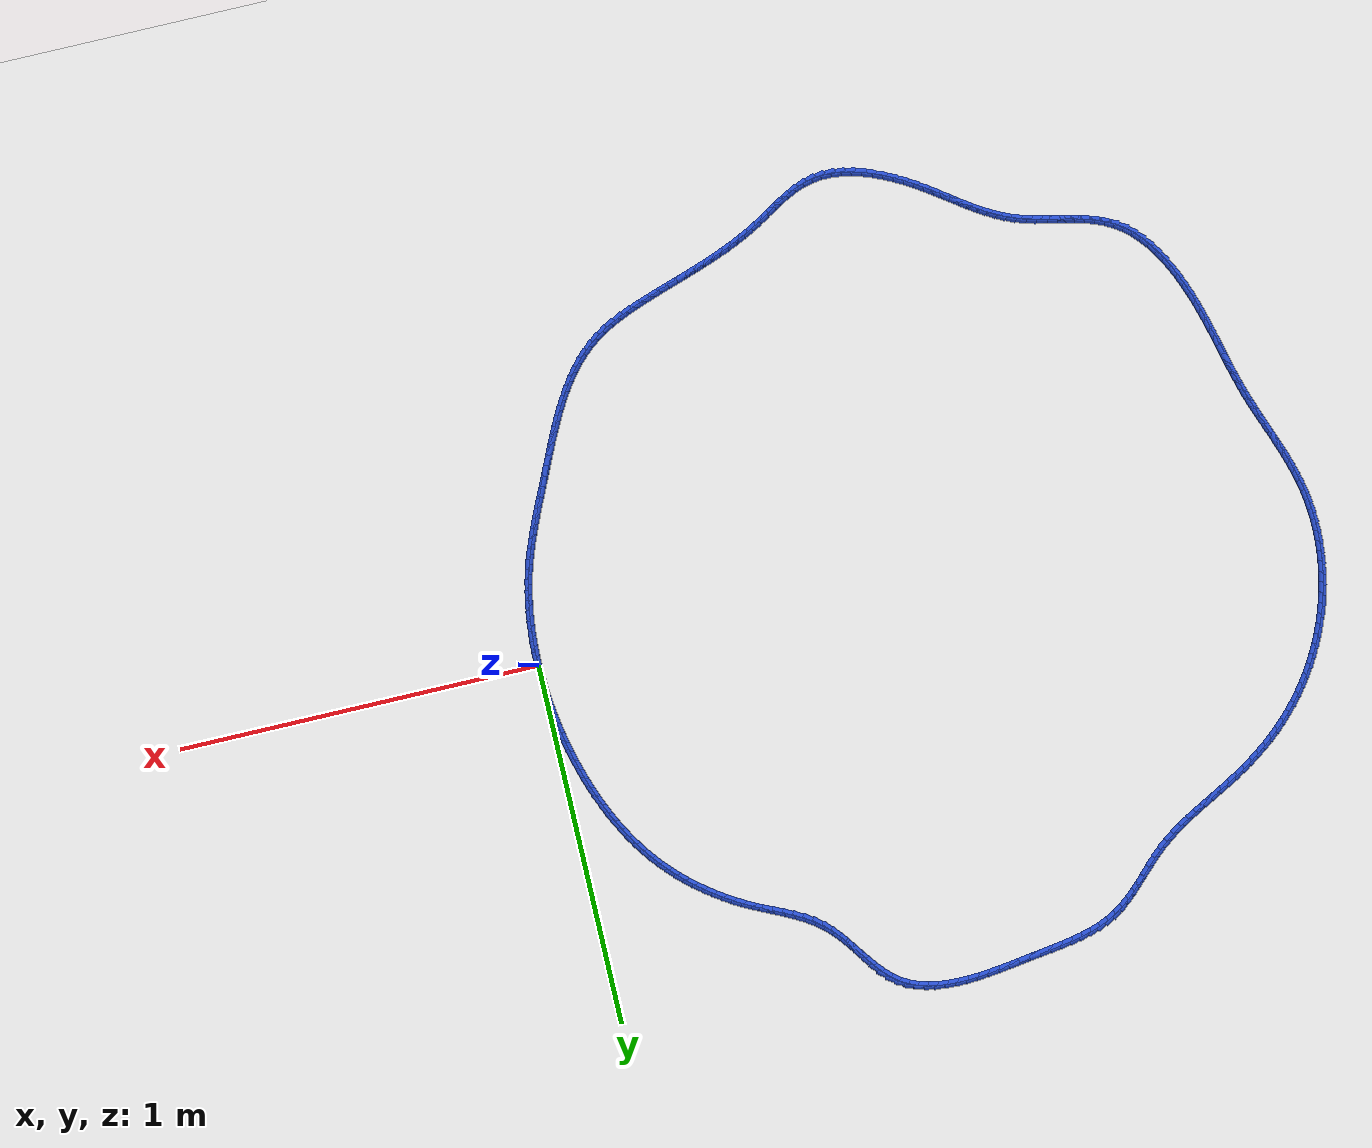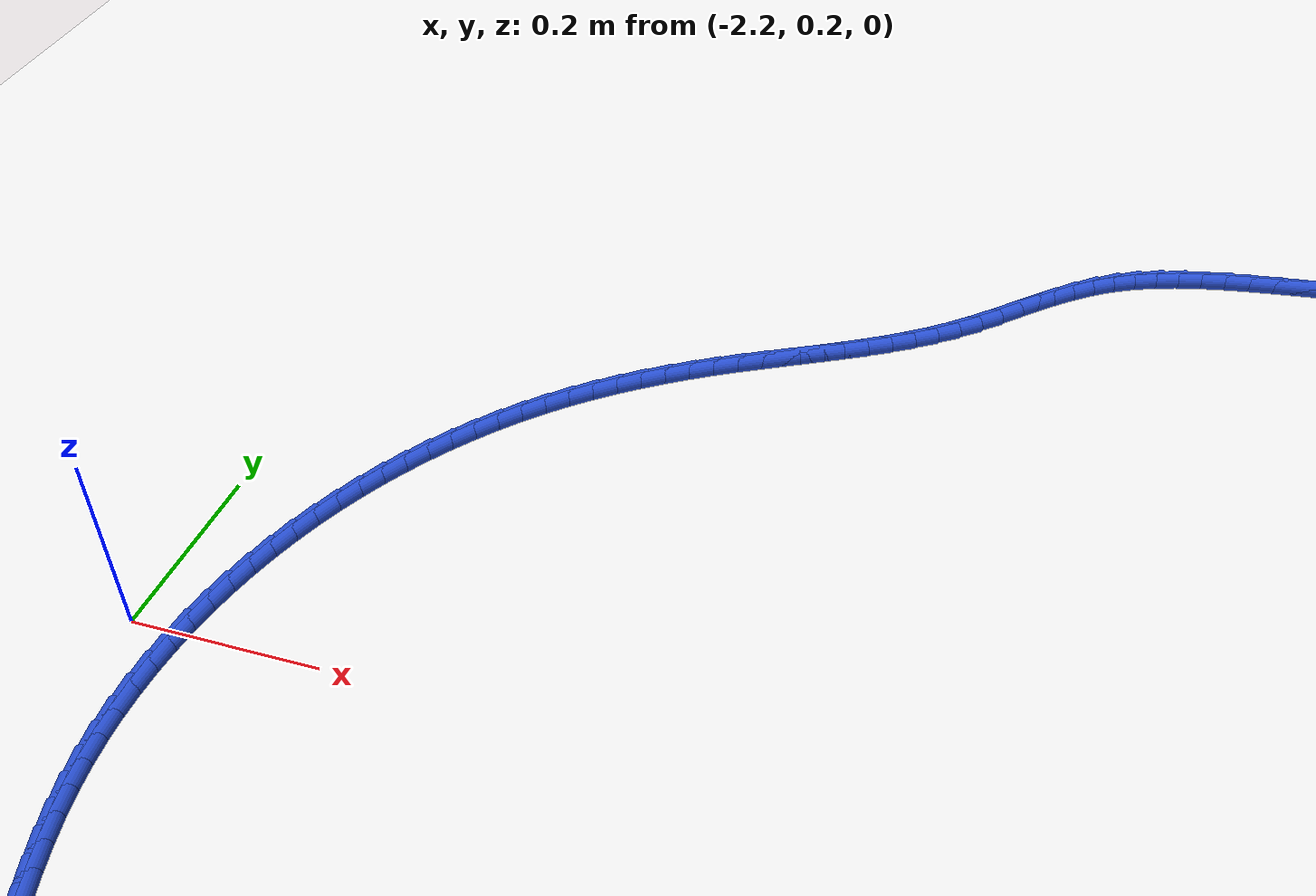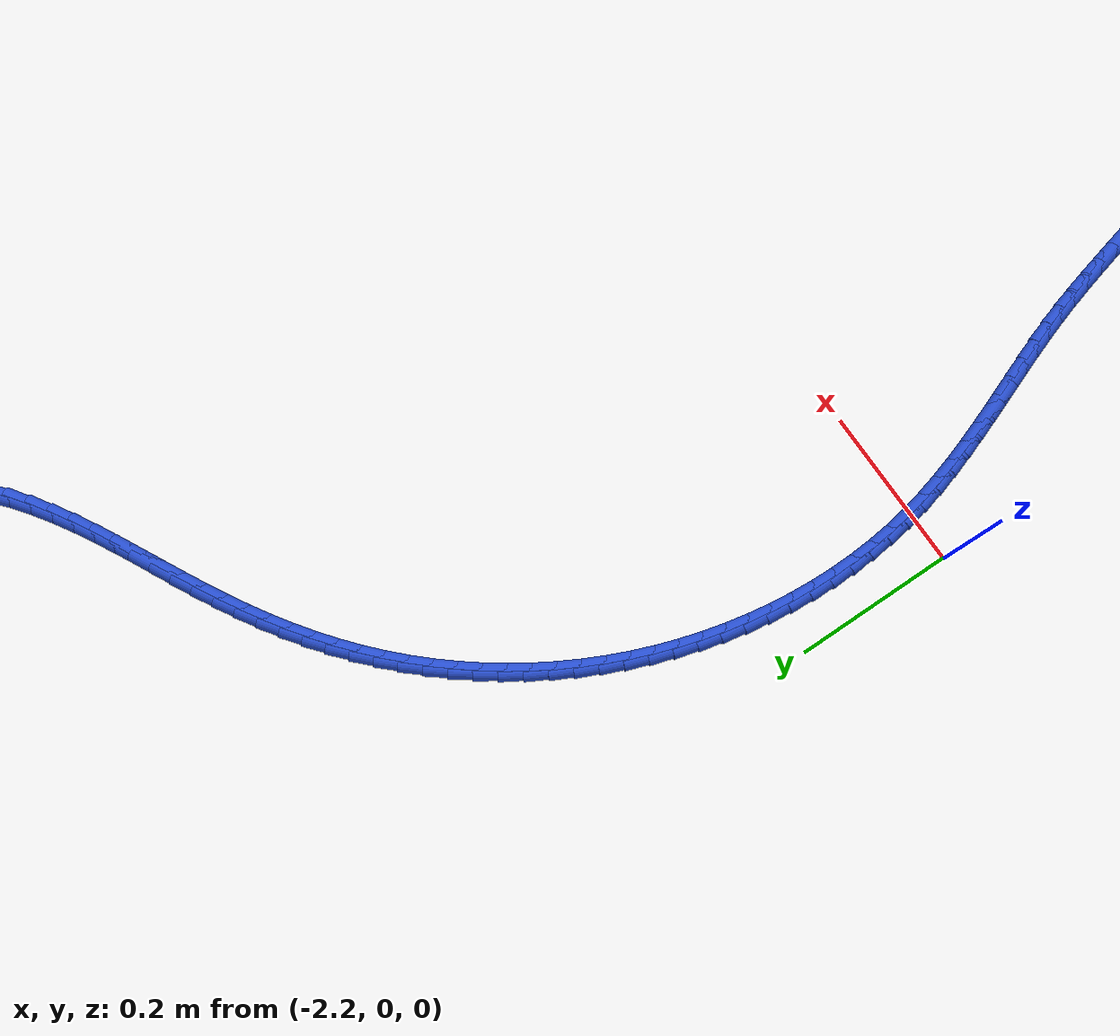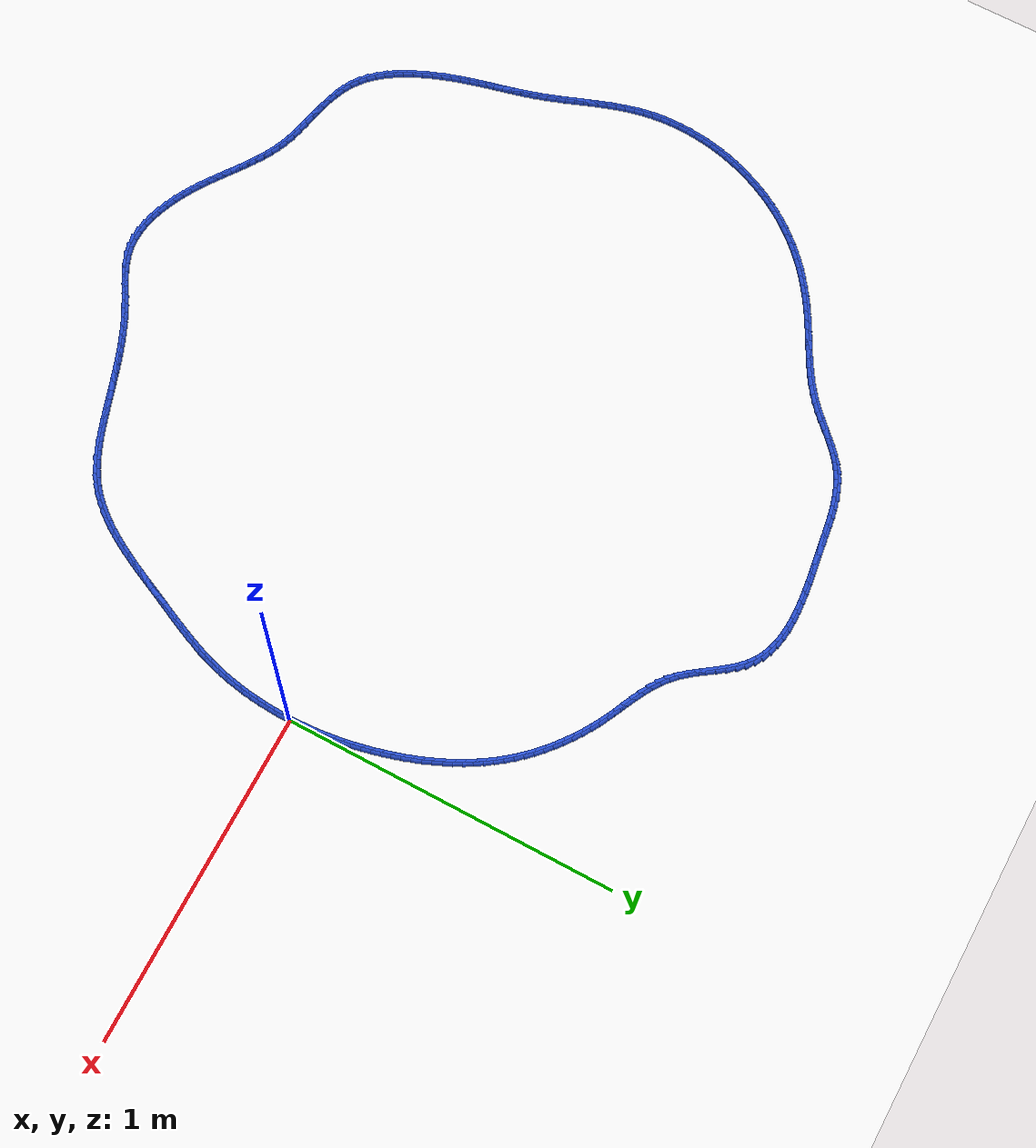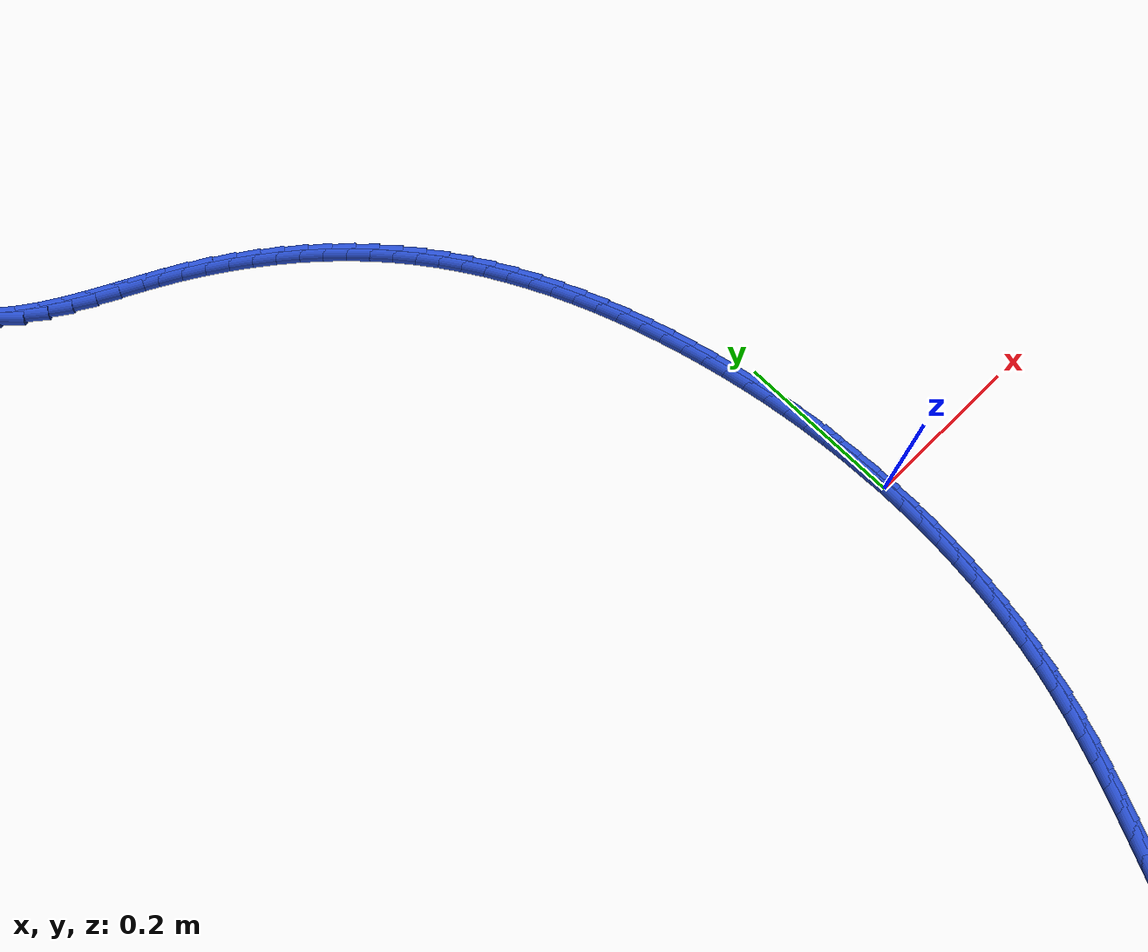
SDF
<sdf version="1.6">
 <world name="default">
  <light name="sun" type="directional">
   <pose>0 0 10 0 -0 0</pose>
   <diffuse>0.8 0.8 0.8 1</diffuse>
   <specular>0.2 0.2 0.2 1</specular>
   <attenuation>
    <range>1000</range>
    <constant>0.9</constant>
    <linear>0.01</linear>
    <quadratic>0.001</quadratic>
   </attenuation>
   <direction>-0.5 0.1 -0.9</direction>
  </light>
  <model name="ground_plane">
   <static>1</static>
   <link name="link">
    <collision name="collision">
     <geometry><plane><normal>0 0 1</normal><size>100 100</size></plane></geometry>
     <surface><friction><ode><mu>100</mu><mu2>50</mu2></ode></friction></surface>
    </collision>
    <visual name="visual">
     <cast_shadows>0</cast_shadows>
     <geometry><plane><normal>0 0 1</normal><size>100 100</size></plane></geometry>
     <material>
      <script><uri>file://media/materials/scripts/gazebo.material</uri><name>Gazebo/WhiteGlow</name></script>
     </material>
    </visual>
   </link>
  </model>
  <gravity>0 0 -9.8</gravity>
  <magnetic_field>6e-06 2.3e-05 -4.2e-05</magnetic_field>
  <atmosphere type="adiabatic"/>
  <physics name="default_physics" default="0" type="ode">
   <max_step_size>0.001</max_step_size>
   <real_time_factor>1</real_time_factor>
   <real_time_update_rate>1000</real_time_update_rate>
  </physics>
  <scene><ambient>0.4 0.4 0.4 1</ambient><background>0.7 0.7 0.7 1</background><shadows>1</shadows></scene>
  <spherical_coordinates>
   <surface_model>EARTH_WGS84</surface_model>
   <latitude_deg>0</latitude_deg>
   <longitude_deg>0</longitude_deg>
   <elevation>0</elevation>
   <heading_deg>0</heading_deg>
  </spherical_coordinates>
  <model name="line">
   <link name="link_0">
    <pose>8.673617379884035e-18 -1.3877787807814457e-17 0.01 0 1.57 -1.5496870519016304</pose>
    <collision name="collision">
     <geometry><cylinder><radius>0.01</radius><length>0.08</length></cylinder></geometry>
    </collision>
    <visual name="visual">
     <material>
      <script><name>Gazebo/Blue</name><uri>file://media/materials/scripts/gazebo.material</uri></script>
     </material>
     <geometry><cylinder><radius>0.01</radius><length>0.08</length></cylinder></geometry>
    </visual>
   </link>
   <link name="link_1">
    <pose>-0.0005935820550612413 0.02811531369161037 0.01 0 1.57 -1.5225756263421197</pose>
    <collision name="collision">
     <geometry><cylinder><radius>0.01</radius><length>0.08</length></cylinder></geometry>
    </collision>
    <visual name="visual">
     <material>
      <script><name>Gazebo/Blue</name><uri>file://media/materials/scripts/gazebo.material</uri></script>
     </material>
     <geometry><cylinder><radius>0.01</radius><length>0.08</length></cylinder></geometry>
    </visual>
   </link>
   <link name="link_2">
    <pose>-0.0019466442927246717 0.05615334160720155 0.01 0 1.57 -1.4957126452156062</pose>
    <collision name="collision">
     <geometry><cylinder><radius>0.01</radius><length>0.08</length></cylinder></geometry>
    </collision>
    <visual name="visual">
     <material>
      <script><name>Gazebo/Blue</name><uri>file://media/materials/scripts/gazebo.material</uri></script>
     </material>
     <geometry><cylinder><radius>0.01</radius><length>0.08</length></cylinder></geometry>
    </visual>
   </link>
   <link name="link_3">
    <pose>-0.004049898525523837 0.08411281689671175 0.01 0 1.57 -1.4691324945821218</pose>
    <collision name="collision">
     <geometry><cylinder><radius>0.01</radius><length>0.08</length></cylinder></geometry>
    </collision>
    <visual name="visual">
     <material>
      <script><name>Gazebo/Blue</name><uri>file://media/materials/scripts/gazebo.material</uri></script>
     </material>
     <geometry><cylinder><radius>0.01</radius><length>0.08</length></cylinder></geometry>
    </visual>
   </link>
   <link name="link_4">
    <pose>-0.006894056565992287 0.11199247271007928 0.01 0 1.57 -1.4428672444223662</pose>
    <collision name="collision">
     <geometry><cylinder><radius>0.01</radius><length>0.08</length></cylinder></geometry>
    </collision>
    <visual name="visual">
     <material>
      <script><name>Gazebo/Blue</name><uri>file://media/materials/scripts/gazebo.material</uri></script>
     </material>
     <geometry><cylinder><radius>0.01</radius><length>0.08</length></cylinder></geometry>
    </visual>
   </link>
   <link name="link_5">
    <pose>-0.010469830226663578 0.13979104219724242 0.01 0 1.57 -1.4169464753337753</pose>
    <collision name="collision">
     <geometry><cylinder><radius>0.01</radius><length>0.08</length></cylinder></geometry>
    </collision>
    <visual name="visual">
     <material>
      <script><name>Gazebo/Blue</name><uri>file://media/materials/scripts/gazebo.material</uri></script>
     </material>
     <geometry><cylinder><radius>0.01</radius><length>0.08</length></cylinder></geometry>
    </visual>
   </link>
   <link name="link_6">
    <pose>-0.01476793132007127 0.1675072585081394 0.01 0 1.57 -1.3913971503743705</pose>
    <collision name="collision">
     <geometry><cylinder><radius>0.01</radius><length>0.08</length></cylinder></geometry>
    </collision>
    <visual name="visual">
     <material>
      <script><name>Gazebo/Blue</name><uri>file://media/materials/scripts/gazebo.material</uri></script>
     </material>
     <geometry><cylinder><radius>0.01</radius><length>0.08</length></cylinder></geometry>
    </visual>
   </link>
   <link name="link_7">
    <pose>-0.0197790716587489 0.19513985479270862 0.01 0 1.57 -1.3662435314455648</pose>
    <collision name="collision">
     <geometry><cylinder><radius>0.01</radius><length>0.08</length></cylinder></geometry>
    </collision>
    <visual name="visual">
     <material>
      <script><name>Gazebo/Blue</name><uri>file://media/materials/scripts/gazebo.material</uri></script>
     </material>
     <geometry><cylinder><radius>0.01</radius><length>0.08</length></cylinder></geometry>
    </visual>
   </link>
   <link name="link_8">
    <pose>-0.02549396305523003 0.22268756420088814 0.01 0 1.57 -1.341507138381807</pose>
    <collision name="collision">
     <geometry><cylinder><radius>0.01</radius><length>0.08</length></cylinder></geometry>
    </collision>
    <visual name="visual">
     <material>
      <script><name>Gazebo/Blue</name><uri>file://media/materials/scripts/gazebo.material</uri></script>
     </material>
     <geometry><cylinder><radius>0.01</radius><length>0.08</length></cylinder></geometry>
    </visual>
   </link>
   <link name="link_9">
    <pose>-0.0319033173220482 0.25014911988261634 0.01 0 1.57 -1.3171224972471922</pose>
    <collision name="collision">
     <geometry><cylinder><radius>0.01</radius><length>0.08</length></cylinder></geometry>
    </collision>
    <visual name="visual">
     <material>
      <script><name>Gazebo/Blue</name><uri>file://media/materials/scripts/gazebo.material</uri></script>
     </material>
     <geometry><cylinder><radius>0.01</radius><length>0.08</length></cylinder></geometry>
    </visual>
   </link>
   <link name="link_10">
    <pose>-0.03899957139405696 0.2775204156260706 0.01 0 1.57 -1.2921599520089047</pose>
    <collision name="collision">
     <geometry><cylinder><radius>0.01</radius><length>0.08</length></cylinder></geometry>
    </collision>
    <visual name="visual">
     <material>
      <script><name>Gazebo/Blue</name><uri>file://media/materials/scripts/gazebo.material</uri></script>
     </material>
     <geometry><cylinder><radius>0.01</radius><length>0.08</length></cylinder></geometry>
    </visual>
   </link>
   <link name="link_11">
    <pose>-0.04679403079307807 0.304766289598792 0.01 0 1.57 -1.2659794614986586</pose>
    <collision name="collision">
     <geometry><cylinder><radius>0.01</radius><length>0.08</length></cylinder></geometry>
    </collision>
    <visual name="visual">
     <material>
      <script><name>Gazebo/Blue</name><uri>file://media/materials/scripts/gazebo.material</uri></script>
     </material>
     <geometry><cylinder><radius>0.01</radius><length>0.08</length></cylinder></geometry>
    </visual>
   </link>
   <link name="link_12">
    <pose>-0.05530963386480234 0.33183243361859144 0.01 0 1.57 -1.2384869728042407</pose>
    <collision name="collision">
     <geometry><cylinder><radius>0.01</radius><length>0.08</length></cylinder></geometry>
    </collision>
    <visual name="visual">
     <material>
      <script><name>Gazebo/Blue</name><uri>file://media/materials/scripts/gazebo.material</uri></script>
     </material>
     <geometry><cylinder><radius>0.01</radius><length>0.08</length></cylinder></geometry>
    </visual>
   </link>
   <link name="link_13">
    <pose>-0.06456948993866612 0.3586642580828249 0.01 0 1.57 -1.209596038206299</pose>
    <collision name="collision">
     <geometry><cylinder><radius>0.01</radius><length>0.08</length></cylinder></geometry>
    </collision>
    <visual name="visual">
     <material>
      <script><name>Gazebo/Blue</name><uri>file://media/materials/scripts/gazebo.material</uri></script>
     </material>
     <geometry><cylinder><radius>0.01</radius><length>0.08</length></cylinder></geometry>
    </visual>
   </link>
   <link name="link_14">
    <pose>-0.07459670834410573 0.3852071733888478 0.01 0 1.57 -1.1792205598598826</pose>
    <collision name="collision">
     <geometry><cylinder><radius>0.01</radius><length>0.08</length></cylinder></geometry>
    </collision>
    <visual name="visual">
     <material>
      <script><name>Gazebo/Blue</name><uri>file://media/materials/scripts/gazebo.material</uri></script>
     </material>
     <geometry><cylinder><radius>0.01</radius><length>0.08</length></cylinder></geometry>
    </visual>
   </link>
   <link name="link_15">
    <pose>-0.08541439841055748 0.41140658993401624 0.01 0 1.57 -1.1472762783633381</pose>
    <collision name="collision">
     <geometry><cylinder><radius>0.01</radius><length>0.08</length></cylinder></geometry>
    </collision>
    <visual name="visual">
     <material>
      <script><name>Gazebo/Blue</name><uri>file://media/materials/scripts/gazebo.material</uri></script>
     </material>
     <geometry><cylinder><radius>0.01</radius><length>0.08</length></cylinder></geometry>
    </visual>
   </link>
   <link name="link_16">
    <pose>-0.09704566946745773 0.43720791811568566 0.01 0 1.57 -1.1136827141171879</pose>
    <collision name="collision">
     <geometry><cylinder><radius>0.01</radius><length>0.08</length></cylinder></geometry>
    </collision>
    <visual name="visual">
     <material>
      <script><name>Gazebo/Blue</name><uri>file://media/materials/scripts/gazebo.material</uri></script>
     </material>
     <geometry><cylinder><radius>0.01</radius><length>0.08</length></cylinder></geometry>
    </visual>
   </link>
   <link name="link_17">
    <pose>-0.10951363084424277 0.4625565683312117 0.01 0 1.57 -1.0783656160031785</pose>
    <collision name="collision">
     <geometry><cylinder><radius>0.01</radius><length>0.08</length></cylinder></geometry>
    </collision>
    <visual name="visual">
     <material>
      <script><name>Gazebo/Blue</name><uri>file://media/materials/scripts/gazebo.material</uri></script>
     </material>
     <geometry><cylinder><radius>0.01</radius><length>0.08</length></cylinder></geometry>
    </visual>
   </link>
   <link name="link_18">
    <pose>-0.12284139187034897 0.4873979509779505 0.01 0 1.57 -1.0412599568365983</pose>
    <collision name="collision">
     <geometry><cylinder><radius>0.01</radius><length>0.08</length></cylinder></geometry>
    </collision>
    <visual name="visual">
     <material>
      <script><name>Gazebo/Blue</name><uri>file://media/materials/scripts/gazebo.material</uri></script>
     </material>
     <geometry><cylinder><radius>0.01</radius><length>0.08</length></cylinder></geometry>
    </visual>
   </link>
   <link name="link_19">
    <pose>-0.1370520618752126 0.5116774764532573 0.01 0 1.57 -1.0023134869240284</pose>
    <collision name="collision">
     <geometry><cylinder><radius>0.01</radius><length>0.08</length></cylinder></geometry>
    </collision>
    <visual name="visual">
     <material>
      <script><name>Gazebo/Blue</name><uri>file://media/materials/scripts/gazebo.material</uri></script>
     </material>
     <geometry><cylinder><radius>0.01</radius><length>0.08</length></cylinder></geometry>
    </visual>
   </link>
   <link name="link_20">
    <pose>-0.15216875018827003 0.5353405551544882 0.01 0 1.57 -0.9614908124573307</pose>
    <collision name="collision">
     <geometry><cylinder><radius>0.01</radius><length>0.08</length></cylinder></geometry>
    </collision>
    <visual name="visual">
     <material>
      <script><name>Gazebo/Blue</name><uri>file://media/materials/scripts/gazebo.material</uri></script>
     </material>
     <geometry><cylinder><radius>0.01</radius><length>0.08</length></cylinder></geometry>
    </visual>
   </link>
   <link name="link_21">
    <pose>-0.16821456613895763 0.5583325974789989 0.01 0 1.57 -0.9187779019538358</pose>
    <collision name="collision">
     <geometry><cylinder><radius>0.01</radius><length>0.08</length></cylinder></geometry>
    </collision>
    <visual name="visual">
     <material>
      <script><name>Gazebo/Blue</name><uri>file://media/materials/scripts/gazebo.material</uri></script>
     </material>
     <geometry><cylinder><radius>0.01</radius><length>0.08</length></cylinder></geometry>
    </visual>
   </link>
   <link name="link_22">
    <pose>-0.18521261905671169 0.5805990138241449 0.01 0 1.57 -0.8745158215303144</pose>
    <collision name="collision">
     <geometry><cylinder><radius>0.01</radius><length>0.08</length></cylinder></geometry>
    </collision>
    <visual name="visual">
     <material>
      <script><name>Gazebo/Blue</name><uri>file://media/materials/scripts/gazebo.material</uri></script>
     </material>
     <geometry><cylinder><radius>0.01</radius><length>0.08</length></cylinder></geometry>
    </visual>
   </link>
   <link name="link_23">
    <pose>-0.20317829433896414 0.6020903434587793 0.01 0 1.57 -0.8306669716038413</pose>
    <collision name="collision">
     <geometry><cylinder><radius>0.01</radius><length>0.08</length></cylinder></geometry>
    </collision>
    <visual name="visual">
     <material>
      <script><name>Gazebo/Blue</name><uri>file://media/materials/scripts/gazebo.material</uri></script>
     </material>
     <geometry><cylinder><radius>0.01</radius><length>0.08</length></cylinder></geometry>
    </visual>
   </link>
   <link name="link_24">
    <pose>-0.22208143795563148 0.6227873648966938 0.01 0 1.57 -0.7879356869457806</pose>
    <collision name="collision">
     <geometry><cylinder><radius>0.01</radius><length>0.08</length></cylinder></geometry>
    </collision>
    <visual name="visual">
     <material>
      <script><name>Gazebo/Blue</name><uri>file://media/materials/scripts/gazebo.material</uri></script>
     </material>
     <geometry><cylinder><radius>0.01</radius><length>0.08</length></cylinder></geometry>
    </visual>
   </link>
   <link name="link_25">
    <pose>-0.2418752635777337 0.6426819008871416 0.01 0 1.57 -0.7463006455793769</pose>
    <collision name="collision">
     <geometry><cylinder><radius>0.01</radius><length>0.08</length></cylinder></geometry>
    </collision>
    <visual name="visual">
     <material>
      <script><name>Gazebo/Blue</name><uri>file://media/materials/scripts/gazebo.material</uri></script>
     </material>
     <geometry><cylinder><radius>0.01</radius><length>0.08</length></cylinder></geometry>
    </visual>
   </link>
   <link name="link_26">
    <pose>-0.2625129603752049 0.6617657904486699 0.01 0 1.57 -0.7057261654845833</pose>
    <collision name="collision">
     <geometry><cylinder><radius>0.01</radius><length>0.08</length></cylinder></geometry>
    </collision>
    <visual name="visual">
     <material>
      <script><name>Gazebo/Blue</name><uri>file://media/materials/scripts/gazebo.material</uri></script>
     </material>
     <geometry><cylinder><radius>0.01</radius><length>0.08</length></cylinder></geometry>
    </visual>
   </link>
   <link name="link_27">
    <pose>-0.28394771751797887 0.6800308725998256 0.01 0 1.57 -0.6661653312461956</pose>
    <collision name="collision">
     <geometry><cylinder><radius>0.01</radius><length>0.08</length></cylinder></geometry>
    </collision>
    <visual name="visual">
     <material>
      <script><name>Gazebo/Blue</name><uri>file://media/materials/scripts/gazebo.material</uri></script>
     </material>
     <geometry><cylinder><radius>0.01</radius><length>0.08</length></cylinder></geometry>
    </visual>
   </link>
   <link name="link_28">
    <pose>-0.3061327241759898 0.6974689863591556 0.01 0 1.57 -0.6275619176166509</pose>
    <collision name="collision">
     <geometry><cylinder><radius>0.01</radius><length>0.08</length></cylinder></geometry>
    </collision>
    <visual name="visual">
     <material>
      <script><name>Gazebo/Blue</name><uri>file://media/materials/scripts/gazebo.material</uri></script>
     </material>
     <geometry><cylinder><radius>0.01</radius><length>0.08</length></cylinder></geometry>
    </visual>
   </link>
   <link name="link_29">
    <pose>-0.3290211695191718 0.7140719707452078 0.01 0 1.57 -0.5898521087856721</pose>
    <collision name="collision">
     <geometry><cylinder><radius>0.01</radius><length>0.08</length></cylinder></geometry>
    </collision>
    <visual name="visual">
     <material>
      <script><name>Gazebo/Blue</name><uri>file://media/materials/scripts/gazebo.material</uri></script>
     </material>
     <geometry><cylinder><radius>0.01</radius><length>0.08</length></cylinder></geometry>
    </visual>
   </link>
   <link name="link_30">
    <pose>-0.35256624271745873 0.7298316647765284 0.01 0 1.57 -0.5529659905632488</pose>
    <collision name="collision">
     <geometry><cylinder><radius>0.01</radius><length>0.08</length></cylinder></geometry>
    </collision>
    <visual name="visual">
     <material>
      <script><name>Gazebo/Blue</name><uri>file://media/materials/scripts/gazebo.material</uri></script>
     </material>
     <geometry><cylinder><radius>0.01</radius><length>0.08</length></cylinder></geometry>
    </visual>
   </link>
   <link name="link_31">
    <pose>-0.3767211329407846 0.744739907471665 0.01 0 1.57 -0.5168288096848384</pose>
    <collision name="collision">
     <geometry><cylinder><radius>0.01</radius><length>0.08</length></cylinder></geometry>
    </collision>
    <visual name="visual">
     <material>
      <script><name>Gazebo/Blue</name><uri>file://media/materials/scripts/gazebo.material</uri></script>
     </material>
     <geometry><cylinder><radius>0.01</radius><length>0.08</length></cylinder></geometry>
    </visual>
   </link>
   <link name="link_32">
    <pose>-0.40143902935908365 0.7587885378491649 0.01 0 1.57 -0.4814641617050005</pose>
    <collision name="collision">
     <geometry><cylinder><radius>0.01</radius><length>0.08</length></cylinder></geometry>
    </collision>
    <visual name="visual">
     <material>
      <script><name>Gazebo/Blue</name><uri>file://media/materials/scripts/gazebo.material</uri></script>
     </material>
     <geometry><cylinder><radius>0.01</radius><length>0.08</length></cylinder></geometry>
    </visual>
   </link>
   <link name="link_33">
    <pose>-0.42667170668410437 0.7719719372036912 0.01 0 1.57 -0.45327145851608164</pose>
    <collision name="collision">
     <geometry><cylinder><radius>0.01</radius><length>0.08</length></cylinder></geometry>
    </collision>
    <visual name="visual">
     <material>
      <script><name>Gazebo/Blue</name><uri>file://media/materials/scripts/gazebo.material</uri></script>
     </material>
     <geometry><cylinder><radius>0.01</radius><length>0.08</length></cylinder></geometry>
    </visual>
   </link>
   <link name="link_34">
    <pose>-0.45228100469497945 0.7844461313617761 0.01 0 1.57 -0.4423971228522923</pose>
    <collision name="collision">
     <geometry><cylinder><radius>0.01</radius><length>0.08</length></cylinder></geometry>
    </collision>
    <visual name="visual">
     <material>
      <script><name>Gazebo/Blue</name><uri>file://media/materials/scripts/gazebo.material</uri></script>
     </material>
     <geometry><cylinder><radius>0.01</radius><length>0.08</length></cylinder></geometry>
    </visual>
   </link>
   <link name="link_35">
    <pose>-0.47798636943449774 0.7966230775014626 0.01 0 1.57 -0.4497587900691112</pose>
    <collision name="collision">
     <geometry><cylinder><radius>0.01</radius><length>0.08</length></cylinder></geometry>
    </collision>
    <visual name="visual">
     <material>
      <script><name>Gazebo/Blue</name><uri>file://media/materials/scripts/gazebo.material</uri></script>
     </material>
     <geometry><cylinder><radius>0.01</radius><length>0.08</length></cylinder></geometry>
    </visual>
   </link>
   <link name="link_36">
    <pose>-0.5034946412111633 0.8089373897146083 0.01 0 1.57 -0.47563905081938845</pose>
    <collision name="collision">
     <geometry><cylinder><radius>0.01</radius><length>0.08</length></cylinder></geometry>
    </collision>
    <visual name="visual">
     <material>
      <script><name>Gazebo/Blue</name><uri>file://media/materials/scripts/gazebo.material</uri></script>
     </material>
     <geometry><cylinder><radius>0.01</radius><length>0.08</length></cylinder></geometry>
    </visual>
   </link>
   <link name="link_37">
    <pose>-0.5285126603334803 0.821823682093072 0.01 0 1.57 -0.5205304839110462</pose>
    <collision name="collision">
     <geometry><cylinder><radius>0.01</radius><length>0.08</length></cylinder></geometry>
    </collision>
    <visual name="visual">
     <material>
      <script><name>Gazebo/Blue</name><uri>file://media/materials/scripts/gazebo.material</uri></script>
     </material>
     <geometry><cylinder><radius>0.01</radius><length>0.08</length></cylinder></geometry>
    </visual>
   </link>
   <link name="link_38">
    <pose>-0.5527472671099526 0.8357165687287116 0.01 0 1.57 -0.5848692271867266</pose>
    <collision name="collision">
     <geometry><cylinder><radius>0.01</radius><length>0.08</length></cylinder></geometry>
    </collision>
    <visual name="visual">
     <material>
      <script><name>Gazebo/Blue</name><uri>file://media/materials/scripts/gazebo.material</uri></script>
     </material>
     <geometry><cylinder><radius>0.01</radius><length>0.08</length></cylinder></geometry>
    </visual>
   </link>
   <link name="link_39">
    <pose>-0.5759053018490848 0.8510506637133854 0.01 0 1.57 -0.6685332507930792</pose>
    <collision name="collision">
     <geometry><cylinder><radius>0.01</radius><length>0.08</length></cylinder></geometry>
    </collision>
    <visual name="visual">
     <material>
      <script><name>Gazebo/Blue</name><uri>file://media/materials/scripts/gazebo.material</uri></script>
     </material>
     <geometry><cylinder><radius>0.01</radius><length>0.08</length></cylinder></geometry>
    </visual>
   </link>
   <link name="link_40">
    <pose>-0.5976936048593808 0.8682605811389517 0.01 0 1.57 -0.767831574314445</pose>
    <collision name="collision">
     <geometry><cylinder><radius>0.01</radius><length>0.08</length></cylinder></geometry>
    </collision>
    <visual name="visual">
     <material>
      <script><name>Gazebo/Blue</name><uri>file://media/materials/scripts/gazebo.material</uri></script>
     </material>
     <geometry><cylinder><radius>0.01</radius><length>0.08</length></cylinder></geometry>
    </visual>
   </link>
   <link name="link_41">
    <pose>-0.6178547880938314 0.8877255956304659 0.01 0 1.57 -0.8539294504244181</pose>
    <collision name="collision">
     <geometry><cylinder><radius>0.01</radius><length>0.08</length></cylinder></geometry>
    </collision>
    <visual name="visual">
     <material>
      <script><name>Gazebo/Blue</name><uri>file://media/materials/scripts/gazebo.material</uri></script>
     </material>
     <geometry><cylinder><radius>0.01</radius><length>0.08</length></cylinder></geometry>
    </visual>
   </link>
   <link name="link_42">
    <pose>-0.6365504148397132 0.9091768555166339 0.01 0 1.57 -0.9105657595181395</pose>
    <collision name="collision">
     <geometry><cylinder><radius>0.01</radius><length>0.08</length></cylinder></geometry>
    </collision>
    <visual name="visual">
     <material>
      <script><name>Gazebo/Blue</name><uri>file://media/materials/scripts/gazebo.material</uri></script>
     </material>
     <geometry><cylinder><radius>0.01</radius><length>0.08</length></cylinder></geometry>
    </visual>
   </link>
   <link name="link_43">
    <pose>-0.654213821748301 0.9319250701647842 0.01 0 1.57 -0.9395338326911635</pose>
    <collision name="collision">
     <geometry><cylinder><radius>0.01</radius><length>0.08</length></cylinder></geometry>
    </collision>
    <visual name="visual">
     <material>
      <script><name>Gazebo/Blue</name><uri>file://media/materials/scripts/gazebo.material</uri></script>
     </material>
     <geometry><cylinder><radius>0.01</radius><length>0.08</length></cylinder></geometry>
    </visual>
   </link>
   <link name="link_44">
    <pose>-0.6712829420856306 0.9552738378850482 0.01 0 1.57 -0.9419563553339502</pose>
    <collision name="collision">
     <geometry><cylinder><radius>0.01</radius><length>0.08</length></cylinder></geometry>
    </collision>
    <visual name="visual">
     <material>
      <script><name>Gazebo/Blue</name><uri>file://media/materials/scripts/gazebo.material</uri></script>
     </material>
     <geometry><cylinder><radius>0.01</radius><length>0.08</length></cylinder></geometry>
    </visual>
   </link>
   <link name="link_45">
    <pose>-0.688195709117738 0.9785267569875566 0.01 0 1.57 -0.9174290044999172</pose>
    <collision name="collision">
     <geometry><cylinder><radius>0.01</radius><length>0.08</length></cylinder></geometry>
    </collision>
    <visual name="visual">
     <material>
      <script><name>Gazebo/Blue</name><uri>file://media/materials/scripts/gazebo.material</uri></script>
     </material>
     <geometry><cylinder><radius>0.01</radius><length>0.08</length></cylinder></geometry>
    </visual>
   </link>
   <link name="link_46">
    <pose>-0.7053900561106593 1.0009874257824412 0.01 0 1.57 -0.8638810282687299</pose>
    <collision name="collision">
     <geometry><cylinder><radius>0.01</radius><length>0.08</length></cylinder></geometry>
    </collision>
    <visual name="visual">
     <material>
      <script><name>Gazebo/Blue</name><uri>file://media/materials/scripts/gazebo.material</uri></script>
     </material>
     <geometry><cylinder><radius>0.01</radius><length>0.08</length></cylinder></geometry>
    </visual>
   </link>
   <link name="link_47">
    <pose>-0.7233039163304303 1.0219594425798326 0.01 0 1.57 -0.777887565120833</pose>
    <collision name="collision">
     <geometry><cylinder><radius>0.01</radius><length>0.08</length></cylinder></geometry>
    </collision>
    <visual name="visual">
     <material>
      <script><name>Gazebo/Blue</name><uri>file://media/materials/scripts/gazebo.material</uri></script>
     </material>
     <geometry><cylinder><radius>0.01</radius><length>0.08</length></cylinder></geometry>
    </visual>
   </link>
   <link name="link_48">
    <pose>-0.7423752230430872 1.0407464056898625 0.01 0 1.57 -0.6568701441062793</pose>
    <collision name="collision">
     <geometry><cylinder><radius>0.01</radius><length>0.08</length></cylinder></geometry>
    </collision>
    <visual name="visual">
     <material>
      <script><name>Gazebo/Blue</name><uri>file://media/materials/scripts/gazebo.material</uri></script>
     </material>
     <geometry><cylinder><radius>0.01</radius><length>0.08</length></cylinder></geometry>
    </visual>
   </link>
   <link name="link_49">
    <pose>-0.7630289038564194 1.0566724994362238 0.01 0 1.57 -0.5213517329006125</pose>
    <collision name="collision">
     <geometry><cylinder><radius>0.01</radius><length>0.08</length></cylinder></geometry>
    </collision>
    <visual name="visual">
     <material>
      <script><name>Gazebo/Blue</name><uri>file://media/materials/scripts/gazebo.material</uri></script>
     </material>
     <geometry><cylinder><radius>0.01</radius><length>0.08</length></cylinder></geometry>
    </visual>
   </link>
   <link name="link_50">
    <pose>-0.7853996456039676 1.0695213159174348 0.01 0 1.57 -0.3959674449629047</pose>
    <collision name="collision">
     <geometry><cylinder><radius>0.01</radius><length>0.08</length></cylinder></geometry>
    </collision>
    <visual name="visual">
     <material>
      <script><name>Gazebo/Blue</name><uri>file://media/materials/scripts/gazebo.material</uri></script>
     </material>
     <geometry><cylinder><radius>0.01</radius><length>0.08</length></cylinder></geometry>
    </visual>
   </link>
   <link name="link_51">
    <pose>-0.8093367486322516 1.0795281713955316 0.01 0 1.57 -0.28481988546648906</pose>
    <collision name="collision">
     <geometry><cylinder><radius>0.01</radius><length>0.08</length></cylinder></geometry>
    </collision>
    <visual name="visual">
     <material>
      <script><name>Gazebo/Blue</name><uri>file://media/materials/scripts/gazebo.material</uri></script>
     </material>
     <geometry><cylinder><radius>0.01</radius><length>0.08</length></cylinder></geometry>
    </visual>
   </link>
   <link name="link_52">
    <pose>-0.8346774785735722 1.0869474312868068 0.01 0 1.57 -0.18905138566288446</pose>
    <collision name="collision">
     <geometry><cylinder><radius>0.01</radius><length>0.08</length></cylinder></geometry>
    </collision>
    <visual name="visual">
     <material>
      <script><name>Gazebo/Blue</name><uri>file://media/materials/scripts/gazebo.material</uri></script>
     </material>
     <geometry><cylinder><radius>0.01</radius><length>0.08</length></cylinder></geometry>
    </visual>
   </link>
   <link name="link_53">
    <pose>-0.8612591010602298 1.0920334610075533 0.01 0 1.57 -0.10829442609271123</pose>
    <collision name="collision">
     <geometry><cylinder><radius>0.01</radius><length>0.08</length></cylinder></geometry>
    </collision>
    <visual name="visual">
     <material>
      <script><name>Gazebo/Blue</name><uri>file://media/materials/scripts/gazebo.material</uri></script>
     </material>
     <geometry><cylinder><radius>0.01</radius><length>0.08</length></cylinder></geometry>
    </visual>
   </link>
   <link name="link_54">
    <pose>-0.8889188817245257 1.095040625974064 0.01 0 1.57 -0.04136421979315932</pose>
    <collision name="collision">
     <geometry><cylinder><radius>0.01</radius><length>0.08</length></cylinder></geometry>
    </collision>
    <visual name="visual">
     <material>
      <script><name>Gazebo/Blue</name><uri>file://media/materials/scripts/gazebo.material</uri></script>
     </material>
     <geometry><cylinder><radius>0.01</radius><length>0.08</length></cylinder></geometry>
    </visual>
   </link>
   <link name="link_55">
    <pose>-0.9174940861987597 1.096223291602632 0.01 0 1.57 0.013210827645202894</pose>
    <collision name="collision">
     <geometry><cylinder><radius>0.01</radius><length>0.08</length></cylinder></geometry>
    </collision>
    <visual name="visual">
     <material>
      <script><name>Gazebo/Blue</name><uri>file://media/materials/scripts/gazebo.material</uri></script>
     </material>
     <geometry><cylinder><radius>0.01</radius><length>0.08</length></cylinder></geometry>
    </visual>
   </link>
   <link name="link_56">
    <pose>-0.9468219801152331 1.0958358233095495 0.01 0 1.57 0.05686907043063197</pose>
    <collision name="collision">
     <geometry><cylinder><radius>0.01</radius><length>0.08</length></cylinder></geometry>
    </collision>
    <visual name="visual">
     <material>
      <script><name>Gazebo/Blue</name><uri>file://media/materials/scripts/gazebo.material</uri></script>
     </material>
     <geometry><cylinder><radius>0.01</radius><length>0.08</length></cylinder></geometry>
    </visual>
   </link>
   <link name="link_57">
    <pose>-0.9767398291062461 1.0941325865111104 0.01 0 1.57 0.09085589678049677</pose>
    <collision name="collision">
     <geometry><cylinder><radius>0.01</radius><length>0.08</length></cylinder></geometry>
    </collision>
    <visual name="visual">
     <material>
      <script><name>Gazebo/Blue</name><uri>file://media/materials/scripts/gazebo.material</uri></script>
     </material>
     <geometry><cylinder><radius>0.01</radius><length>0.08</length></cylinder></geometry>
    </visual>
   </link>
   <link name="link_58">
    <pose>-1.0070848988040995 1.091367946623606 0.01 0 1.57 0.1161597627894585</pose>
    <collision name="collision">
     <geometry><cylinder><radius>0.01</radius><length>0.08</length></cylinder></geometry>
    </collision>
    <visual name="visual">
     <material>
      <script><name>Gazebo/Blue</name><uri>file://media/materials/scripts/gazebo.material</uri></script>
     </material>
     <geometry><cylinder><radius>0.01</radius><length>0.08</length></cylinder></geometry>
    </visual>
   </link>
   <link name="link_59">
    <pose>-1.0376944548410938 1.0877962690633303 0.01 0 1.57 0.1334954730307414</pose>
    <collision name="collision">
     <geometry><cylinder><radius>0.01</radius><length>0.08</length></cylinder></geometry>
    </collision>
    <visual name="visual">
     <material>
      <script><name>Gazebo/Blue</name><uri>file://media/materials/scripts/gazebo.material</uri></script>
     </material>
     <geometry><cylinder><radius>0.01</radius><length>0.08</length></cylinder></geometry>
    </visual>
   </link>
   <link name="link_60">
    <pose>-1.0684057628495305 1.0836719192465762 0.01 0 1.57 0.14330484486759168</pose>
    <collision name="collision">
     <geometry><cylinder><radius>0.01</radius><length>0.08</length></cylinder></geometry>
    </collision>
    <visual name="visual">
     <material>
      <script><name>Gazebo/Blue</name><uri>file://media/materials/scripts/gazebo.material</uri></script>
     </material>
     <geometry><cylinder><radius>0.01</radius><length>0.08</length></cylinder></geometry>
    </visual>
   </link>
   <link name="link_61">
    <pose>-1.0990560884617087 1.0792492625896357 0.01 0 1.57 0.14575799966463604</pose>
    <collision name="collision">
     <geometry><cylinder><radius>0.01</radius><length>0.08</length></cylinder></geometry>
    </collision>
    <visual name="visual">
     <material>
      <script><name>Gazebo/Blue</name><uri>file://media/materials/scripts/gazebo.material</uri></script>
     </material>
     <geometry><cylinder><radius>0.01</radius><length>0.08</length></cylinder></geometry>
    </visual>
   </link>
   <link name="link_62">
    <pose>-1.1294826973099303 1.0747826645088026 0.01 0 1.57 0.14203251685983956</pose>
    <collision name="collision">
     <geometry><cylinder><radius>0.01</radius><length>0.08</length></cylinder></geometry>
    </collision>
    <visual name="visual">
     <material>
      <script><name>Gazebo/Blue</name><uri>file://media/materials/scripts/gazebo.material</uri></script>
     </material>
     <geometry><cylinder><radius>0.01</radius><length>0.08</length></cylinder></geometry>
    </visual>
   </link>
   <link name="link_63">
    <pose>-1.1595283705377428 1.070486272278852 0.01 0 1.57 0.14298898115756992</pose>
    <collision name="collision">
     <geometry><cylinder><radius>0.01</radius><length>0.08</length></cylinder></geometry>
    </collision>
    <visual name="visual">
     <material>
      <script><name>Gazebo/Blue</name><uri>file://media/materials/scripts/gazebo.material</uri></script>
     </material>
     <geometry><cylinder><radius>0.01</radius><length>0.08</length></cylinder></geometry>
    </visual>
   </link>
   <link name="link_64">
    <pose>-1.1890829248731665 1.0662312579347422 0.01 0 1.57 0.15460730312139717</pose>
    <collision name="collision">
     <geometry><cylinder><radius>0.01</radius><length>0.08</length></cylinder></geometry>
    </collision>
    <visual name="visual">
     <material>
      <script><name>Gazebo/Blue</name><uri>file://media/materials/scripts/gazebo.material</uri></script>
     </material>
     <geometry><cylinder><radius>0.01</radius><length>0.08</length></cylinder></geometry>
    </visual>
   </link>
   <link name="link_65">
    <pose>-1.2180599903508489 1.0617151510523783 0.01 0 1.57 0.17756633891431411</pose>
    <collision name="collision">
     <geometry><cylinder><radius>0.01</radius><length>0.08</length></cylinder></geometry>
    </collision>
    <visual name="visual">
     <material>
      <script><name>Gazebo/Blue</name><uri>file://media/materials/scripts/gazebo.material</uri></script>
     </material>
     <geometry><cylinder><radius>0.01</radius><length>0.08</length></cylinder></geometry>
    </visual>
   </link>
   <link name="link_66">
    <pose>-1.246373382038112 1.0566341319818258 0.01 0 1.57 0.2125940894117049</pose>
    <collision name="collision">
     <geometry><cylinder><radius>0.01</radius><length>0.08</length></cylinder></geometry>
    </collision>
    <visual name="visual">
     <material>
      <script><name>Gazebo/Blue</name><uri>file://media/materials/scripts/gazebo.material</uri></script>
     </material>
     <geometry><cylinder><radius>0.01</radius><length>0.08</length></cylinder></geometry>
    </visual>
   </link>
   <link name="link_67">
    <pose>-1.2739369150022763 1.0506843810731485 0.01 0 1.57 0.26042674896760604</pose>
    <collision name="collision">
     <geometry><cylinder><radius>0.01</radius><length>0.08</length></cylinder></geometry>
    </collision>
    <visual name="visual">
     <material>
      <script><name>Gazebo/Blue</name><uri>file://media/materials/scripts/gazebo.material</uri></script>
     </material>
     <geometry><cylinder><radius>0.01</radius><length>0.08</length></cylinder></geometry>
    </visual>
   </link>
   <link name="link_68">
    <pose>-1.300664404310664 1.043562078676412 0.01 0 1.57 0.32164312924781424</pose>
    <collision name="collision">
     <geometry><cylinder><radius>0.01</radius><length>0.08</length></cylinder></geometry>
    </collision>
    <visual name="visual">
     <material>
      <script><name>Gazebo/Blue</name><uri>file://media/materials/scripts/gazebo.material</uri></script>
     </material>
     <geometry><cylinder><radius>0.01</radius><length>0.08</length></cylinder></geometry>
    </visual>
   </link>
   <link name="link_69">
    <pose>-1.326469665030597 1.034963405141681 0.01 0 1.57 0.3963997188025557</pose>
    <collision name="collision">
     <geometry><cylinder><radius>0.01</radius><length>0.08</length></cylinder></geometry>
    </collision>
    <visual name="visual">
     <material>
      <script><name>Gazebo/Blue</name><uri>file://media/materials/scripts/gazebo.material</uri></script>
     </material>
     <geometry><cylinder><radius>0.01</radius><length>0.08</length></cylinder></geometry>
    </visual>
   </link>
   <link name="link_70">
    <pose>-1.3512665122293972 1.0245845408190208 0.01 0 1.57 0.4840816189618638</pose>
    <collision name="collision">
     <geometry><cylinder><radius>0.01</radius><length>0.08</length></cylinder></geometry>
    </collision>
    <visual name="visual">
     <material>
      <script><name>Gazebo/Blue</name><uri>file://media/materials/scripts/gazebo.material</uri></script>
     </material>
     <geometry><cylinder><radius>0.01</radius><length>0.08</length></cylinder></geometry>
    </visual>
   </link>
   <link name="link_71">
    <pose>-1.3749687609743855 1.012121666058496 0.01 0 1.57 0.5807861027989323</pose>
    <collision name="collision">
     <geometry><cylinder><radius>0.01</radius><length>0.08</length></cylinder></geometry>
    </collision>
    <visual name="visual">
     <material>
      <script><name>Gazebo/Blue</name><uri>file://media/materials/scripts/gazebo.material</uri></script>
     </material>
     <geometry><cylinder><radius>0.01</radius><length>0.08</length></cylinder></geometry>
    </visual>
   </link>
   <link name="link_72">
    <pose>-1.39751430096481 0.9973251958567998 0.01 0 1.57 0.6645909405233154</pose>
    <collision name="collision">
     <geometry><cylinder><radius>0.01</radius><length>0.08</length></cylinder></geometry>
    </collision>
    <visual name="visual">
     <material>
      <script><name>Gazebo/Blue</name><uri>file://media/materials/scripts/gazebo.material</uri></script>
     </material>
     <geometry><cylinder><radius>0.01</radius><length>0.08</length></cylinder></geometry>
    </visual>
   </link>
   <link name="link_73">
    <pose>-1.4190618301741929 0.9804429758157717 0.01 0 1.57 0.7250321027307001</pose>
    <collision name="collision">
     <geometry><cylinder><radius>0.01</radius><length>0.08</length></cylinder></geometry>
    </collision>
    <visual name="visual">
     <material>
      <script><name>Gazebo/Blue</name><uri>file://media/materials/scripts/gazebo.material</uri></script>
     </material>
     <geometry><cylinder><radius>0.01</radius><length>0.08</length></cylinder></geometry>
    </visual>
   </link>
   <link name="link_74">
    <pose>-1.4398887000804155 0.9619901507798673 0.01 0 1.57 0.7633668413979282</pose>
    <collision name="collision">
     <geometry><cylinder><radius>0.01</radius><length>0.08</length></cylinder></geometry>
    </collision>
    <visual name="visual">
     <material>
      <script><name>Gazebo/Blue</name><uri>file://media/materials/scripts/gazebo.material</uri></script>
     </material>
     <geometry><cylinder><radius>0.01</radius><length>0.08</length></cylinder></geometry>
    </visual>
   </link>
   <link name="link_75">
    <pose>-1.460273400890601 0.9424844308904174 0.01 0 1.57 0.7809245543680977</pose>
    <collision name="collision">
     <geometry><cylinder><radius>0.01</radius><length>0.08</length></cylinder></geometry>
    </collision>
    <visual name="visual">
     <material>
      <script><name>Gazebo/Blue</name><uri>file://media/materials/scripts/gazebo.material</uri></script>
     </material>
     <geometry><cylinder><radius>0.01</radius><length>0.08</length></cylinder></geometry>
    </visual>
   </link>
   <link name="link_76">
    <pose>-1.4804944228118742 0.9224435262887514 0.01 0 1.57 0.7785296125036536</pose>
    <collision name="collision">
     <geometry><cylinder><radius>0.01</radius><length>0.08</length></cylinder></geometry>
    </collision>
    <visual name="visual">
     <material>
      <script><name>Gazebo/Blue</name><uri>file://media/materials/scripts/gazebo.material</uri></script>
     </material>
     <geometry><cylinder><radius>0.01</radius><length>0.08</length></cylinder></geometry>
    </visual>
   </link>
   <link name="link_77">
    <pose>-1.5008302560513567 0.9023851471161988 0.01 0 1.57 0.7563403165326268</pose>
    <collision name="collision">
     <geometry><cylinder><radius>0.01</radius><length>0.08</length></cylinder></geometry>
    </collision>
    <visual name="visual">
     <material>
      <script><name>Gazebo/Blue</name><uri>file://media/materials/scripts/gazebo.material</uri></script>
     </material>
     <geometry><cylinder><radius>0.01</radius><length>0.08</length></cylinder></geometry>
    </visual>
   </link>
   <link name="link_78">
    <pose>-1.5215593908161733 0.882827003514089 0.01 0 1.57 0.7139247877903906</pose>
    <collision name="collision">
     <geometry><cylinder><radius>0.01</radius><length>0.08</length></cylinder></geometry>
    </collision>
    <visual name="visual">
     <material>
      <script><name>Gazebo/Blue</name><uri>file://media/materials/scripts/gazebo.material</uri></script>
     </material>
     <geometry><cylinder><radius>0.01</radius><length>0.08</length></cylinder></geometry>
    </visual>
   </link>
   <link name="link_79">
    <pose>-1.5429599202045285 0.8642860946094303 0.01 0 1.57 0.6583734830817721</pose>
    <collision name="collision">
     <geometry><cylinder><radius>0.01</radius><length>0.08</length></cylinder></geometry>
    </collision>
    <visual name="visual">
     <material>
      <script><name>Gazebo/Blue</name><uri>file://media/materials/scripts/gazebo.material</uri></script>
     </material>
     <geometry><cylinder><radius>0.01</radius><length>0.08</length></cylinder></geometry>
    </visual>
   </link>
   <link name="link_80">
    <pose>-1.565200300263476 0.847083116928187 0.01 0 1.57 0.6082113104159013</pose>
    <collision name="collision">
     <geometry><cylinder><radius>0.01</radius><length>0.08</length></cylinder></geometry>
    </collision>
    <visual name="visual">
     <material>
      <script><name>Gazebo/Blue</name><uri>file://media/materials/scripts/gazebo.material</uri></script>
     </material>
     <geometry><cylinder><radius>0.01</radius><length>0.08</length></cylinder></geometry>
    </visual>
   </link>
   <link name="link_81">
    <pose>-1.5881905058168513 0.8310759623522161 0.01 0 1.57 0.5665418743031984</pose>
    <collision name="collision">
     <geometry><cylinder><radius>0.01</radius><length>0.08</length></cylinder></geometry>
    </collision>
    <visual name="visual">
     <material>
      <script><name>Gazebo/Blue</name><uri>file://media/materials/scripts/gazebo.material</uri></script>
     </material>
     <geometry><cylinder><radius>0.01</radius><length>0.08</length></cylinder></geometry>
    </visual>
   </link>
   <link name="link_82">
    <pose>-1.6118032823021373 0.8160558644092963 0.01 0 1.57 0.5335887879607111</pose>
    <collision name="collision">
     <geometry><cylinder><radius>0.01</radius><length>0.08</length></cylinder></geometry>
    </collision>
    <visual name="visual">
     <material>
      <script><name>Gazebo/Blue</name><uri>file://media/materials/scripts/gazebo.material</uri></script>
     </material>
     <geometry><cylinder><radius>0.01</radius><length>0.08</length></cylinder></geometry>
    </visual>
   </link>
   <link name="link_83">
    <pose>-1.6359113751568182 0.8018140566272048 0.01 0 1.57 0.5094189261070686</pose>
    <collision name="collision">
     <geometry><cylinder><radius>0.01</radius><length>0.08</length></cylinder></geometry>
    </collision>
    <visual name="visual">
     <material>
      <script><name>Gazebo/Blue</name><uri>file://media/materials/scripts/gazebo.material</uri></script>
     </material>
     <geometry><cylinder><radius>0.01</radius><length>0.08</length></cylinder></geometry>
    </visual>
   </link>
   <link name="link_84">
    <pose>-1.66038752981838 0.7881417725337206 0.01 0 1.57 0.4940164376076443</pose>
    <collision name="collision">
     <geometry><cylinder><radius>0.01</radius><length>0.08</length></cylinder></geometry>
    </collision>
    <visual name="visual">
     <material>
      <script><name>Gazebo/Blue</name><uri>file://media/materials/scripts/gazebo.material</uri></script>
     </material>
     <geometry><cylinder><radius>0.01</radius><length>0.08</length></cylinder></geometry>
    </visual>
   </link>
   <link name="link_85">
    <pose>-1.6851044917243057 0.7748302456566213 0.01 0 1.57 0.4873385638721867</pose>
    <collision name="collision">
     <geometry><cylinder><radius>0.01</radius><length>0.08</length></cylinder></geometry>
    </collision>
    <visual name="visual">
     <material>
      <script><name>Gazebo/Blue</name><uri>file://media/materials/scripts/gazebo.material</uri></script>
     </material>
     <geometry><cylinder><radius>0.01</radius><length>0.08</length></cylinder></geometry>
    </visual>
   </link>
   <link name="link_86">
    <pose>-1.7099350063120788 0.7616707095236851 0.01 0 1.57 0.4893509785444931</pose>
    <collision name="collision">
     <geometry><cylinder><radius>0.01</radius><length>0.08</length></cylinder></geometry>
    </collision>
    <visual name="visual">
     <material>
      <script><name>Gazebo/Blue</name><uri>file://media/materials/scripts/gazebo.material</uri></script>
     </material>
     <geometry><cylinder><radius>0.01</radius><length>0.08</length></cylinder></geometry>
    </visual>
   </link>
   <link name="link_87">
    <pose>-1.7347518190191844 0.7484543976626903 0.01 0 1.57 0.5000428308767667</pose>
    <collision name="collision">
     <geometry><cylinder><radius>0.01</radius><length>0.08</length></cylinder></geometry>
    </collision>
    <visual name="visual">
     <material>
      <script><name>Gazebo/Blue</name><uri>file://media/materials/scripts/gazebo.material</uri></script>
     </material>
     <geometry><cylinder><radius>0.01</radius><length>0.08</length></cylinder></geometry>
    </visual>
   </link>
   <link name="link_88">
    <pose>-1.7594276752831066 0.734972543601415 0.01 0 1.57 0.5193824767309676</pose>
    <collision name="collision">
     <geometry><cylinder><radius>0.01</radius><length>0.08</length></cylinder></geometry>
    </collision>
    <visual name="visual">
     <material>
      <script><name>Gazebo/Blue</name><uri>file://media/materials/scripts/gazebo.material</uri></script>
     </material>
     <geometry><cylinder><radius>0.01</radius><length>0.08</length></cylinder></geometry>
    </visual>
   </link>
   <link name="link_89">
    <pose>-1.78383571410854 0.7210174388630552 0.01 0 1.57 0.5450853156954637</pose>
    <collision name="collision">
     <geometry><cylinder><radius>0.01</radius><length>0.08</length></cylinder></geometry>
    </collision>
    <visual name="visual">
     <material>
      <script><name>Gazebo/Blue</name><uri>file://media/materials/scripts/gazebo.material</uri></script>
     </material>
     <geometry><cylinder><radius>0.01</radius><length>0.08</length></cylinder></geometry>
    </visual>
   </link>
   <link name="link_90">
    <pose>-1.8078719125217473 0.7064427686071344 0.01 0 1.57 0.5736780438581209</pose>
    <collision name="collision">
     <geometry><cylinder><radius>0.01</radius><length>0.08</length></cylinder></geometry>
    </collision>
    <visual name="visual">
     <material>
      <script><name>Gazebo/Blue</name><uri>file://media/materials/scripts/gazebo.material</uri></script>
     </material>
     <geometry><cylinder><radius>0.01</radius><length>0.08</length></cylinder></geometry>
    </visual>
   </link>
   <link name="link_91">
    <pose>-1.8314672073428457 0.6911961976254953 0.01 0 1.57 0.604919640788983</pose>
    <collision name="collision">
     <geometry><cylinder><radius>0.01</radius><length>0.08</length></cylinder></geometry>
    </collision>
    <visual name="visual">
     <material>
      <script><name>Gazebo/Blue</name><uri>file://media/materials/scripts/gazebo.material</uri></script>
     </material>
     <geometry><cylinder><radius>0.01</radius><length>0.08</length></cylinder></geometry>
    </visual>
   </link>
   <link name="link_92">
    <pose>-1.8545554919399216 0.6752333385626538 0.01 0 1.57 0.6388562066959235</pose>
    <collision name="collision">
     <geometry><cylinder><radius>0.01</radius><length>0.08</length></cylinder></geometry>
    </collision>
    <visual name="visual">
     <material>
      <script><name>Gazebo/Blue</name><uri>file://media/materials/scripts/gazebo.material</uri></script>
     </material>
     <geometry><cylinder><radius>0.01</radius><length>0.08</length></cylinder></geometry>
    </visual>
   </link>
   <link name="link_93">
    <pose>-1.8770706596810611 0.6585098040631249 0.01 0 1.57 0.6755165076006285</pose>
    <collision name="collision">
     <geometry><cylinder><radius>0.01</radius><length>0.08</length></cylinder></geometry>
    </collision>
    <visual name="visual">
     <material>
      <script><name>Gazebo/Blue</name><uri>file://media/materials/scripts/gazebo.material</uri></script>
     </material>
     <geometry><cylinder><radius>0.01</radius><length>0.08</length></cylinder></geometry>
    </visual>
   </link>
   <link name="link_94">
    <pose>-1.8989466039343488 0.6409812067714242 0.01 0 1.57 0.7148986950571599</pose>
    <collision name="collision">
     <geometry><cylinder><radius>0.01</radius><length>0.08</length></cylinder></geometry>
    </collision>
    <visual name="visual">
     <material>
      <script><name>Gazebo/Blue</name><uri>file://media/materials/scripts/gazebo.material</uri></script>
     </material>
     <geometry><cylinder><radius>0.01</radius><length>0.08</length></cylinder></geometry>
    </visual>
   </link>
   <link name="link_95">
    <pose>-1.9201172896293586 0.622603303947651 0.01 0 1.57 0.7560971403130712</pose>
    <collision name="collision">
     <geometry><cylinder><radius>0.01</radius><length>0.08</length></cylinder></geometry>
    </collision>
    <visual name="visual">
     <material>
      <script><name>Gazebo/Blue</name><uri>file://media/materials/scripts/gazebo.material</uri></script>
     </material>
     <geometry><cylinder><radius>0.01</radius><length>0.08</length></cylinder></geometry>
    </visual>
   </link>
   <link name="link_96">
    <pose>-1.94052808471754 0.6033548967366082 0.01 0 1.57 0.797281574676467</pose>
    <collision name="collision">
     <geometry><cylinder><radius>0.01</radius><length>0.08</length></cylinder></geometry>
    </collision>
    <visual name="visual">
     <material>
      <script><name>Gazebo/Blue</name><uri>file://media/materials/scripts/gazebo.material</uri></script>
     </material>
     <geometry><cylinder><radius>0.01</radius><length>0.08</length></cylinder></geometry>
    </visual>
   </link>
   <link name="link_97">
    <pose>-1.9601481585913791 0.5832628856087918 0.01 0 1.57 0.8382699062775709</pose>
    <collision name="collision">
     <geometry><cylinder><radius>0.01</radius><length>0.08</length></cylinder></geometry>
    </collision>
    <visual name="visual">
     <material>
      <script><name>Gazebo/Blue</name><uri>file://media/materials/scripts/gazebo.material</uri></script>
     </material>
     <geometry><cylinder><radius>0.01</radius><length>0.08</length></cylinder></geometry>
    </visual>
   </link>
   <link name="link_98">
    <pose>-1.978949661363941 0.5623601946468629 0.01 0 1.57 0.8791133885800223</pose>
    <collision name="collision">
     <geometry><cylinder><radius>0.01</radius><length>0.08</length></cylinder></geometry>
    </collision>
    <visual name="visual">
     <material>
      <script><name>Gazebo/Blue</name><uri>file://media/materials/scripts/gazebo.material</uri></script>
     </material>
     <geometry><cylinder><radius>0.01</radius><length>0.08</length></cylinder></geometry>
    </visual>
   </link>
   <link name="link_99">
    <pose>-1.9969047431482894 0.5406797479334824 0.01 0 1.57 0.9198639503953323</pose>
    <collision name="collision">
     <geometry><cylinder><radius>0.01</radius><length>0.08</length></cylinder></geometry>
    </collision>
    <visual name="visual">
     <material>
      <script><name>Gazebo/Blue</name><uri>file://media/materials/scripts/gazebo.material</uri></script>
     </material>
     <geometry><cylinder><radius>0.01</radius><length>0.08</length></cylinder></geometry>
    </visual>
   </link>
   <link name="link_100">
    <pose>-2.0139855540574887 0.5182544695513112 0.01 0 1.57 0.9605735222294822</pose>
    <collision name="collision">
     <geometry><cylinder><radius>0.01</radius><length>0.08</length></cylinder></geometry>
    </collision>
    <visual name="visual">
     <material>
      <script><name>Gazebo/Blue</name><uri>file://media/materials/scripts/gazebo.material</uri></script>
     </material>
     <geometry><cylinder><radius>0.01</radius><length>0.08</length></cylinder></geometry>
    </visual>
   </link>
   <link name="link_101">
    <pose>-2.030164244204602 0.4951172835830111 0.01 0 1.57 1.001293382315827</pose>
    <collision name="collision">
     <geometry><cylinder><radius>0.01</radius><length>0.08</length></cylinder></geometry>
    </collision>
    <visual name="visual">
     <material>
      <script><name>Gazebo/Blue</name><uri>file://media/materials/scripts/gazebo.material</uri></script>
     </material>
     <geometry><cylinder><radius>0.01</radius><length>0.08</length></cylinder></geometry>
    </visual>
   </link>
   <link name="link_102">
    <pose>-2.0454129637026943 0.47130111411124304 0.01 0 1.57 1.042073513890765</pose>
    <collision name="collision">
     <geometry><cylinder><radius>0.01</radius><length>0.08</length></cylinder></geometry>
    </collision>
    <visual name="visual">
     <material>
      <script><name>Gazebo/Blue</name><uri>file://media/materials/scripts/gazebo.material</uri></script>
     </material>
     <geometry><cylinder><radius>0.01</radius><length>0.08</length></cylinder></geometry>
    </visual>
   </link>
   <link name="link_103">
    <pose>-2.0597038626648287 0.44683888521866805 0.01 0 1.57 1.0829619658160066</pose>
    <collision name="collision">
     <geometry><cylinder><radius>0.01</radius><length>0.08</length></cylinder></geometry>
    </collision>
    <visual name="visual">
     <material>
      <script><name>Gazebo/Blue</name><uri>file://media/materials/scripts/gazebo.material</uri></script>
     </material>
     <geometry><cylinder><radius>0.01</radius><length>0.08</length></cylinder></geometry>
    </visual>
   </link>
   <link name="link_104">
    <pose>-2.07300909120407 0.421763520987947 0.01 0 1.57 1.1240042019081184</pose>
    <collision name="collision">
     <geometry><cylinder><radius>0.01</radius><length>0.08</length></cylinder></geometry>
    </collision>
    <visual name="visual">
     <material>
      <script><name>Gazebo/Blue</name><uri>file://media/materials/scripts/gazebo.material</uri></script>
     </material>
     <geometry><cylinder><radius>0.01</radius><length>0.08</length></cylinder></geometry>
    </visual>
   </link>
   <link name="link_105">
    <pose>-2.085300799505579 0.3961079458754709 0.01 0 1.57 1.1651364799601855</pose>
    <collision name="collision">
     <geometry><cylinder><radius>0.01</radius><length>0.08</length></cylinder></geometry>
    </collision>
    <visual name="visual">
     <material>
      <script><name>Gazebo/Blue</name><uri>file://media/materials/scripts/gazebo.material</uri></script>
     </material>
     <geometry><cylinder><radius>0.01</radius><length>0.08</length></cylinder></geometry>
    </visual>
   </link>
   <link name="link_106">
    <pose>-2.0965521572744685 0.369910369241611 0.01 0 1.57 1.2060684940001019</pose>
    <collision name="collision">
     <geometry><cylinder><radius>0.01</radius><length>0.08</length></cylinder></geometry>
    </collision>
    <visual name="visual">
     <material>
      <script><name>Gazebo/Blue</name><uri>file://media/materials/scripts/gazebo.material</uri></script>
     </material>
     <geometry><cylinder><radius>0.01</radius><length>0.08</length></cylinder></geometry>
    </visual>
   </link>
   <link name="link_107">
    <pose>-2.1067399182539646 0.3432275790897737 0.01 0 1.57 1.2468562923244804</pose>
    <collision name="collision">
     <geometry><cylinder><radius>0.01</radius><length>0.08</length></cylinder></geometry>
    </collision>
    <visual name="visual">
     <material>
      <script><name>Gazebo/Blue</name><uri>file://media/materials/scripts/gazebo.material</uri></script>
     </material>
     <geometry><cylinder><radius>0.01</radius><length>0.08</length></cylinder></geometry>
    </visual>
   </link>
   <link name="link_108">
    <pose>-2.115841623333502 0.31612044376736786 0.01 0 1.57 1.2876421689406725</pose>
    <collision name="collision">
     <geometry><cylinder><radius>0.01</radius><length>0.08</length></cylinder></geometry>
    </collision>
    <visual name="visual">
     <material>
      <script><name>Gazebo/Blue</name><uri>file://media/materials/scripts/gazebo.material</uri></script>
     </material>
     <geometry><cylinder><radius>0.01</radius><length>0.08</length></cylinder></geometry>
    </visual>
   </link>
   <link name="link_109">
    <pose>-2.1238348134025116 0.28864983162180324 0.01 0 1.57 1.3285674898002886</pose>
    <collision name="collision">
     <geometry><cylinder><radius>0.01</radius><length>0.08</length></cylinder></geometry>
    </collision>
    <visual name="visual">
     <material>
      <script><name>Gazebo/Blue</name><uri>file://media/materials/scripts/gazebo.material</uri></script>
     </material>
     <geometry><cylinder><radius>0.01</radius><length>0.08</length></cylinder></geometry>
    </visual>
   </link>
   <link name="link_110">
    <pose>-2.1306970293504275 0.26087661100048865 0.01 0 1.57 1.3697724400306166</pose>
    <collision name="collision">
     <geometry><cylinder><radius>0.01</radius><length>0.08</length></cylinder></geometry>
    </collision>
    <visual name="visual">
     <material>
      <script><name>Gazebo/Blue</name><uri>file://media/materials/scripts/gazebo.material</uri></script>
     </material>
     <geometry><cylinder><radius>0.01</radius><length>0.08</length></cylinder></geometry>
    </visual>
   </link>
   <link name="link_111">
    <pose>-2.136405812066684 0.23286165025083336 0.01 0 1.57 1.4113956860137278</pose>
    <collision name="collision">
     <geometry><cylinder><radius>0.01</radius><length>0.08</length></cylinder></geometry>
    </collision>
    <visual name="visual">
     <material>
      <script><name>Gazebo/Blue</name><uri>file://media/materials/scripts/gazebo.material</uri></script>
     </material>
     <geometry><cylinder><radius>0.01</radius><length>0.08</length></cylinder></geometry>
    </visual>
   </link>
   <link name="link_112">
    <pose>-2.1409387024407134 0.2046658177202461 0.01 0 1.57 1.4535738826807318</pose>
    <collision name="collision">
     <geometry><cylinder><radius>0.01</radius><length>0.08</length></cylinder></geometry>
    </collision>
    <visual name="visual">
     <material>
      <script><name>Gazebo/Blue</name><uri>file://media/materials/scripts/gazebo.material</uri></script>
     </material>
     <geometry><cylinder><radius>0.01</radius><length>0.08</length></cylinder></geometry>
    </visual>
   </link>
   <link name="link_113">
    <pose>-2.144273241361949 0.17634998175613684 0.01 0 1.57 1.496440955202695</pose>
    <collision name="collision">
     <geometry><cylinder><radius>0.01</radius><length>0.08</length></cylinder></geometry>
    </collision>
    <visual name="visual">
     <material>
      <script><name>Gazebo/Blue</name><uri>file://media/materials/scripts/gazebo.material</uri></script>
     </material>
     <geometry><cylinder><radius>0.01</radius><length>0.08</length></cylinder></geometry>
    </visual>
   </link>
   <link name="link_114">
    <pose>-2.146386969719824 0.14797501070591434 0.01 0 1.57 1.5401270829545246</pose>
    <collision name="collision">
     <geometry><cylinder><radius>0.01</radius><length>0.08</length></cylinder></geometry>
    </collision>
    <visual name="visual">
     <material>
      <script><name>Gazebo/Blue</name><uri>file://media/materials/scripts/gazebo.material</uri></script>
     </material>
     <geometry><cylinder><radius>0.01</radius><length>0.08</length></cylinder></geometry>
    </visual>
   </link>
   <link name="link_115">
    <pose>-2.147257428403772 0.1196017729169874 0.01 0 1.57 -1.55683533993788</pose>
    <collision name="collision">
     <geometry><cylinder><radius>0.01</radius><length>0.08</length></cylinder></geometry>
    </collision>
    <visual name="visual">
     <material>
      <script><name>Gazebo/Blue</name><uri>file://media/materials/scripts/gazebo.material</uri></script>
     </material>
     <geometry><cylinder><radius>0.01</radius><length>0.08</length></cylinder></geometry>
    </visual>
   </link>
   <link name="link_116">
    <pose>-2.1468621583032257 0.09129113673676593 0.01 0 1.57 -1.5111429146714528</pose>
    <collision name="collision">
     <geometry><cylinder><radius>0.01</radius><length>0.08</length></cylinder></geometry>
    </collision>
    <visual name="visual">
     <material>
      <script><name>Gazebo/Blue</name><uri>file://media/materials/scripts/gazebo.material</uri></script>
     </material>
     <geometry><cylinder><radius>0.01</radius><length>0.08</length></cylinder></geometry>
    </visual>
   </link>
   <link name="link_117">
    <pose>-2.1451787003076195 0.06310397051265884 0.01 0 1.57 -1.4642794817210734</pose>
    <collision name="collision">
     <geometry><cylinder><radius>0.01</radius><length>0.08</length></cylinder></geometry>
    </collision>
    <visual name="visual">
     <material>
      <script><name>Gazebo/Blue</name><uri>file://media/materials/scripts/gazebo.material</uri></script>
     </material>
     <geometry><cylinder><radius>0.01</radius><length>0.08</length></cylinder></geometry>
    </visual>
   </link>
   <link name="link_118">
    <pose>-2.142184595306385 0.03510114259207512 0.01 0 1.57 -1.4161483744494114</pose>
    <collision name="collision">
     <geometry><cylinder><radius>0.01</radius><length>0.08</length></cylinder></geometry>
    </collision>
    <visual name="visual">
     <material>
      <script><name>Gazebo/Blue</name><uri>file://media/materials/scripts/gazebo.material</uri></script>
     </material>
     <geometry><cylinder><radius>0.01</radius><length>0.08</length></cylinder></geometry>
    </visual>
   </link>
   <link name="link_119">
    <pose>-2.137857384365703 0.007343521241138437 0.01 0 1.57 -1.368073335322618</pose>
    <collision name="collision">
     <geometry><cylinder><radius>0.01</radius><length>0.08</length></cylinder></geometry>
    </collision>
    <visual name="visual">
     <material>
      <script><name>Gazebo/Blue</name><uri>file://media/materials/scripts/gazebo.material</uri></script>
     </material>
     <geometry><cylinder><radius>0.01</radius><length>0.08</length></cylinder></geometry>
    </visual>
   </link>
   <link name="link_120">
    <pose>-2.132211342810018 -0.020124919238106588 0.01 0 1.57 -1.3254312612473649</pose>
    <collision name="collision">
     <geometry><cylinder><radius>0.01</radius><length>0.08</length></cylinder></geometry>
    </collision>
    <visual name="visual">
     <material>
      <script><name>Gazebo/Blue</name><uri>file://media/materials/scripts/gazebo.material</uri></script>
     </material>
     <geometry><cylinder><radius>0.01</radius><length>0.08</length></cylinder></geometry>
    </visual>
   </link>
   <link name="link_121">
    <pose>-2.125400307607433 -0.04732438848270661 0.01 0 1.57 -1.2896020849260996</pose>
    <collision name="collision">
     <geometry><cylinder><radius>0.01</radius><length>0.08</length></cylinder></geometry>
    </collision>
    <visual name="visual">
     <material>
      <script><name>Gazebo/Blue</name><uri>file://media/materials/scripts/gazebo.material</uri></script>
     </material>
     <geometry><cylinder><radius>0.01</radius><length>0.08</length></cylinder></geometry>
    </visual>
   </link>
   <link name="link_122">
    <pose>-2.117611253952663 -0.07429033629070539 0.01 0 1.57 -1.2606062650558665</pose>
    <collision name="collision">
     <geometry><cylinder><radius>0.01</radius><length>0.08</length></cylinder></geometry>
    </collision>
    <visual name="visual">
     <material>
      <script><name>Gazebo/Blue</name><uri>file://media/materials/scripts/gazebo.material</uri></script>
     </material>
     <geometry><cylinder><radius>0.01</radius><length>0.08</length></cylinder></geometry>
    </visual>
   </link>
   <link name="link_123">
    <pose>-2.1090311570404254 -0.10105821246014679 0.01 0 1.57 -1.2384030128663903</pose>
    <collision name="collision">
     <geometry><cylinder><radius>0.01</radius><length>0.08</length></cylinder></geometry>
    </collision>
    <visual name="visual">
     <material>
      <script><name>Gazebo/Blue</name><uri>file://media/materials/scripts/gazebo.material</uri></script>
     </material>
     <geometry><cylinder><radius>0.01</radius><length>0.08</length></cylinder></geometry>
    </visual>
   </link>
   <link name="link_124">
    <pose>-2.099846992065436 -0.12766346678907464 0.01 0 1.57 -1.2229307689024895</pose>
    <collision name="collision">
     <geometry><cylinder><radius>0.01</radius><length>0.08</length></cylinder></geometry>
    </collision>
    <visual name="visual">
     <material>
      <script><name>Gazebo/Blue</name><uri>file://media/materials/scripts/gazebo.material</uri></script>
     </material>
     <geometry><cylinder><radius>0.01</radius><length>0.08</length></cylinder></geometry>
    </visual>
   </link>
   <link name="link_125">
    <pose>-2.090245734222409 -0.1541415490755334 0.01 0 1.57 -1.2141374890386685</pose>
    <collision name="collision">
     <geometry><cylinder><radius>0.01</radius><length>0.08</length></cylinder></geometry>
    </collision>
    <visual name="visual">
     <material>
      <script><name>Gazebo/Blue</name><uri>file://media/materials/scripts/gazebo.material</uri></script>
     </material>
     <geometry><cylinder><radius>0.01</radius><length>0.08</length></cylinder></geometry>
    </visual>
   </link>
   <link name="link_126">
    <pose>-2.0804143587060615 -0.18052790911756547 0.01 0 1.57 -1.2120011785899536</pose>
    <collision name="collision">
     <geometry><cylinder><radius>0.01</radius><length>0.08</length></cylinder></geometry>
    </collision>
    <visual name="visual">
     <material>
      <script><name>Gazebo/Blue</name><uri>file://media/materials/scripts/gazebo.material</uri></script>
     </material>
     <geometry><cylinder><radius>0.01</radius><length>0.08</length></cylinder></geometry>
    </visual>
   </link>
   <link name="link_127">
    <pose>-2.07053984071111 -0.20685799671321545 0.01 0 1.57 -1.2165415430570916</pose>
    <collision name="collision">
     <geometry><cylinder><radius>0.01</radius><length>0.08</length></cylinder></geometry>
    </collision>
    <visual name="visual">
     <material>
      <script><name>Gazebo/Blue</name><uri>file://media/materials/scripts/gazebo.material</uri></script>
     </material>
     <geometry><cylinder><radius>0.01</radius><length>0.08</length></cylinder></geometry>
    </visual>
   </link>
   <link name="link_128">
    <pose>-2.0608091554322696 -0.23316726166052706 0.01 0 1.57 -1.2278233505292329</pose>
    <collision name="collision">
     <geometry><cylinder><radius>0.01</radius><length>0.08</length></cylinder></geometry>
    </collision>
    <visual name="visual">
     <material>
      <script><name>Gazebo/Blue</name><uri>file://media/materials/scripts/gazebo.material</uri></script>
     </material>
     <geometry><cylinder><radius>0.01</radius><length>0.08</length></cylinder></geometry>
    </visual>
   </link>
   <link name="link_129">
    <pose>-2.051409278064257 -0.2594911537575442 0.01 0 1.57 -1.2459514486265786</pose>
    <collision name="collision">
     <geometry><cylinder><radius>0.01</radius><length>0.08</length></cylinder></geometry>
    </collision>
    <visual name="visual">
     <material>
      <script><name>Gazebo/Blue</name><uri>file://media/materials/scripts/gazebo.material</uri></script>
     </material>
     <geometry><cylinder><radius>0.01</radius><length>0.08</length></cylinder></geometry>
    </visual>
   </link>
   <link name="link_130">
    <pose>-2.0425271838017864 -0.2858651228023106 0.01 0 1.57 -1.2703431306392174</pose>
    <collision name="collision">
     <geometry><cylinder><radius>0.01</radius><length>0.08</length></cylinder></geometry>
    </collision>
    <visual name="visual">
     <material>
      <script><name>Gazebo/Blue</name><uri>file://media/materials/scripts/gazebo.material</uri></script>
     </material>
     <geometry><cylinder><radius>0.01</radius><length>0.08</length></cylinder></geometry>
    </visual>
   </link>
   <link name="link_131">
    <pose>-2.034329586784084 -0.3123232475309808 0.01 0 1.57 -1.293619150744632</pose>
    <collision name="collision">
     <geometry><cylinder><radius>0.01</radius><length>0.08</length></cylinder></geometry>
    </collision>
    <visual name="visual">
     <material>
      <script><name>Gazebo/Blue</name><uri>file://media/materials/scripts/gazebo.material</uri></script>
     </material>
     <geometry><cylinder><radius>0.01</radius><length>0.08</length></cylinder></geometry>
    </visual>
   </link>
   <link name="link_132">
    <pose>-2.0267726512450266 -0.33888535880643567 0.01 0 1.57 -1.3112104932519524</pose>
    <collision name="collision">
     <geometry><cylinder><radius>0.01</radius><length>0.08</length></cylinder></geometry>
    </collision>
    <visual name="visual">
     <material>
      <script><name>Gazebo/Blue</name><uri>file://media/materials/scripts/gazebo.material</uri></script>
     </material>
     <geometry><cylinder><radius>0.01</radius><length>0.08</length></cylinder></geometry>
    </visual>
   </link>
   <link name="link_133">
    <pose>-2.0196876962882198 -0.3655628392446075 0.01 0 1.57 -1.322931237999049</pose>
    <collision name="collision">
     <geometry><cylinder><radius>0.01</radius><length>0.08</length></cylinder></geometry>
    </collision>
    <visual name="visual">
     <material>
      <script><name>Gazebo/Blue</name><uri>file://media/materials/scripts/gazebo.material</uri></script>
     </material>
     <geometry><cylinder><radius>0.01</radius><length>0.08</length></cylinder></geometry>
    </visual>
   </link>
   <link name="link_134">
    <pose>-2.0129044027488243 -0.3923669606001068 0.01 0 1.57 -1.3287387235723722</pose>
    <collision name="collision">
     <geometry><cylinder><radius>0.01</radius><length>0.08</length></cylinder></geometry>
    </collision>
    <visual name="visual">
     <material>
      <script><name>Gazebo/Blue</name><uri>file://media/materials/scripts/gazebo.material</uri></script>
     </material>
     <geometry><cylinder><radius>0.01</radius><length>0.08</length></cylinder></geometry>
    </visual>
   </link>
   <link name="link_135">
    <pose>-2.0062524514620046 -0.4193089946275442 0.01 0 1.57 -1.3286641500457739</pose>
    <collision name="collision">
     <geometry><cylinder><radius>0.01</radius><length>0.08</length></cylinder></geometry>
    </collision>
    <visual name="visual">
     <material>
      <script><name>Gazebo/Blue</name><uri>file://media/materials/scripts/gazebo.material</uri></script>
     </material>
     <geometry><cylinder><radius>0.01</radius><length>0.08</length></cylinder></geometry>
    </visual>
   </link>
   <link name="link_136">
    <pose>-1.9995615232629216 -0.4464002130815291 0.01 0 1.57 -1.3228047166897816</pose>
    <collision name="collision">
     <geometry><cylinder><radius>0.01</radius><length>0.08</length></cylinder></geometry>
    </collision>
    <visual name="visual">
     <material>
      <script><name>Gazebo/Blue</name><uri>file://media/materials/scripts/gazebo.material</uri></script>
     </material>
     <geometry><cylinder><radius>0.01</radius><length>0.08</length></cylinder></geometry>
    </visual>
   </link>
   <link name="link_137">
    <pose>-1.9926612989867385 -0.47365188771667205 0.01 0 1.57 -1.3113200431945644</pose>
    <collision name="collision">
     <geometry><cylinder><radius>0.01</radius><length>0.08</length></cylinder></geometry>
    </collision>
    <visual name="visual">
     <material>
      <script><name>Gazebo/Blue</name><uri>file://media/materials/scripts/gazebo.material</uri></script>
     </material>
     <geometry><cylinder><radius>0.01</radius><length>0.08</length></cylinder></geometry>
    </visual>
   </link>
   <link name="link_138">
    <pose>-1.985381459468618 -0.501075290287583 0.01 0 1.57 -1.2944324174126878</pose>
    <collision name="collision">
     <geometry><cylinder><radius>0.01</radius><length>0.08</length></cylinder></geometry>
    </collision>
    <visual name="visual">
     <material>
      <script><name>Gazebo/Blue</name><uri>file://media/materials/scripts/gazebo.material</uri></script>
     </material>
     <geometry><cylinder><radius>0.01</radius><length>0.08</length></cylinder></geometry>
    </visual>
   </link>
   <link name="link_139">
    <pose>-1.9775516855437227 -0.5286816925488721 0.01 0 1.57 -1.2724308612212958</pose>
    <collision name="collision">
     <geometry><cylinder><radius>0.01</radius><length>0.08</length></cylinder></geometry>
    </collision>
    <visual name="visual">
     <material>
      <script><name>Gazebo/Blue</name><uri>file://media/materials/scripts/gazebo.material</uri></script>
     </material>
     <geometry><cylinder><radius>0.01</radius><length>0.08</length></cylinder></geometry>
    </visual>
   </link>
   <link name="link_140">
    <pose>-1.969001935746869 -0.5564815790947628 0.01 0 1.57 -1.2457137619730718</pose>
    <collision name="collision">
     <geometry><cylinder><radius>0.01</radius><length>0.08</length></cylinder></geometry>
    </collision>
    <visual name="visual">
     <material>
      <script><name>Gazebo/Blue</name><uri>file://media/materials/scripts/gazebo.material</uri></script>
     </material>
     <geometry><cylinder><radius>0.01</radius><length>0.08</length></cylinder></geometry>
    </visual>
   </link>
   <link name="link_141">
    <pose>-1.959592551722807 -0.5843993113279495 0.01 0 1.57 -1.214320206307619</pose>
    <collision name="collision">
     <geometry><cylinder><radius>0.01</radius><length>0.08</length></cylinder></geometry>
    </collision>
    <visual name="visual">
     <material>
      <script><name>Gazebo/Blue</name><uri>file://media/materials/scripts/gazebo.material</uri></script>
     </material>
     <geometry><cylinder><radius>0.01</radius><length>0.08</length></cylinder></geometry>
    </visual>
   </link>
   <link name="link_142">
    <pose>-1.9492412271886992 -0.6121966819236919 0.01 0 1.57 -1.1777500423077247</pose>
    <collision name="collision">
     <geometry><cylinder><radius>0.01</radius><length>0.08</length></cylinder></geometry>
    </collision>
    <visual name="visual">
     <material>
      <script><name>Gazebo/Blue</name><uri>file://media/materials/scripts/gazebo.material</uri></script>
     </material>
     <geometry><cylinder><radius>0.01</radius><length>0.08</length></cylinder></geometry>
    </visual>
   </link>
   <link name="link_143">
    <pose>-1.9378720198089927 -0.639617444473952 0.01 0 1.57 -1.1353343986133293</pose>
    <collision name="collision">
     <geometry><cylinder><radius>0.01</radius><length>0.08</length></cylinder></geometry>
    </collision>
    <visual name="visual">
     <material>
      <script><name>Gazebo/Blue</name><uri>file://media/materials/scripts/gazebo.material</uri></script>
     </material>
     <geometry><cylinder><radius>0.01</radius><length>0.08</length></cylinder></geometry>
    </visual>
   </link>
   <link name="link_144">
    <pose>-1.9254089872481366 -0.666405352570692 0.01 0 1.57 -1.086262495747468</pose>
    <collision name="collision">
     <geometry><cylinder><radius>0.01</radius><length>0.08</length></cylinder></geometry>
    </collision>
    <visual name="visual">
     <material>
      <script><name>Gazebo/Blue</name><uri>file://media/materials/scripts/gazebo.material</uri></script>
     </material>
     <geometry><cylinder><radius>0.01</radius><length>0.08</length></cylinder></geometry>
    </visual>
   </link>
   <link name="link_145">
    <pose>-1.911776187170578 -0.6923041598058738 0.01 0 1.57 -1.0295919838617977</pose>
    <collision name="collision">
     <geometry><cylinder><radius>0.01</radius><length>0.08</length></cylinder></geometry>
    </collision>
    <visual name="visual">
     <material>
      <script><name>Gazebo/Blue</name><uri>file://media/materials/scripts/gazebo.material</uri></script>
     </material>
     <geometry><cylinder><radius>0.01</radius><length>0.08</length></cylinder></geometry>
    </visual>
   </link>
   <link name="link_146">
    <pose>-1.8968976772407649 -0.7170576197714592 0.01 0 1.57 -0.9642829619869212</pose>
    <collision name="collision">
     <geometry><cylinder><radius>0.01</radius><length>0.08</length></cylinder></geometry>
    </collision>
    <visual name="visual">
     <material>
      <script><name>Gazebo/Blue</name><uri>file://media/materials/scripts/gazebo.material</uri></script>
     </material>
     <geometry><cylinder><radius>0.01</radius><length>0.08</length></cylinder></geometry>
    </visual>
   </link>
   <link name="link_147">
    <pose>-1.880697515123144 -0.740409486059411 0.01 0 1.57 -0.8892754898691357</pose>
    <collision name="collision">
     <geometry><cylinder><radius>0.01</radius><length>0.08</length></cylinder></geometry>
    </collision>
    <visual name="visual">
     <material>
      <script><name>Gazebo/Blue</name><uri>file://media/materials/scripts/gazebo.material</uri></script>
     </material>
     <geometry><cylinder><radius>0.01</radius><length>0.08</length></cylinder></geometry>
    </visual>
   </link>
   <link name="link_148">
    <pose>-1.8630997584821642 -0.7621035122616897 0.01 0 1.57 -0.8036361336653858</pose>
    <collision name="collision">
     <geometry><cylinder><radius>0.01</radius><length>0.08</length></cylinder></geometry>
    </collision>
    <visual name="visual">
     <material>
      <script><name>Gazebo/Blue</name><uri>file://media/materials/scripts/gazebo.material</uri></script>
     </material>
     <geometry><cylinder><radius>0.01</radius><length>0.08</length></cylinder></geometry>
    </visual>
   </link>
   <link name="link_149">
    <pose>-1.8440284649822742 -0.7818834519702588 0.01 0 1.57 -0.706796742413469</pose>
    <collision name="collision">
     <geometry><cylinder><radius>0.01</radius><length>0.08</length></cylinder></geometry>
    </collision>
    <visual name="visual">
     <material>
      <script><name>Gazebo/Blue</name><uri>file://media/materials/scripts/gazebo.material</uri></script>
     </material>
     <geometry><cylinder><radius>0.01</radius><length>0.08</length></cylinder></geometry>
    </visual>
   </link>
   <link name="link_150">
    <pose>-1.8234076922879192 -0.7994930587770788 0.01 0 1.57 -0.5988851631076626</pose>
    <collision name="collision">
     <geometry><cylinder><radius>0.01</radius><length>0.08</length></cylinder></geometry>
    </collision>
    <visual name="visual">
     <material>
      <script><name>Gazebo/Blue</name><uri>file://media/materials/scripts/gazebo.material</uri></script>
     </material>
     <geometry><cylinder><radius>0.01</radius><length>0.08</length></cylinder></geometry>
    </visual>
   </link>
   <link name="link_151">
    <pose>-1.801161509992557 -0.8146761099230229 0.01 0 1.57 -0.48688744629694564</pose>
    <collision name="collision">
     <geometry><cylinder><radius>0.01</radius><length>0.08</length></cylinder></geometry>
    </collision>
    <visual name="visual">
     <material>
      <script><name>Gazebo/Blue</name><uri>file://media/materials/scripts/gazebo.material</uri></script>
     </material>
     <geometry><cylinder><radius>0.01</radius><length>0.08</length></cylinder></geometry>
    </visual>
   </link>
   <link name="link_152">
    <pose>-1.7772846387019041 -0.827316446219467 0.01 0 1.57 -0.392103172799685</pose>
    <collision name="collision">
     <geometry><cylinder><radius>0.01</radius><length>0.08</length></cylinder></geometry>
    </collision>
    <visual name="visual">
     <material>
      <script><name>Gazebo/Blue</name><uri>file://media/materials/scripts/gazebo.material</uri></script>
     </material>
     <geometry><cylinder><radius>0.01</radius><length>0.08</length></cylinder></geometry>
    </visual>
   </link>
   <link name="link_153">
    <pose>-1.7520090685388958 -0.83776828837314 0.01 0 1.57 -0.31897546764901613</pose>
    <collision name="collision">
     <geometry><cylinder><radius>0.01</radius><length>0.08</length></cylinder></geometry>
    </collision>
    <visual name="visual">
     <material>
      <script><name>Gazebo/Blue</name><uri>file://media/materials/scripts/gazebo.material</uri></script>
     </material>
     <geometry><cylinder><radius>0.01</radius><length>0.08</length></cylinder></geometry>
    </visual>
   </link>
   <link name="link_154">
    <pose>-1.725616543296873 -0.84648449229074 0.01 0 1.57 -0.2665144061350039</pose>
    <collision name="collision">
     <geometry><cylinder><radius>0.01</radius><length>0.08</length></cylinder></geometry>
    </collision>
    <visual name="visual">
     <material>
      <script><name>Gazebo/Blue</name><uri>file://media/materials/scripts/gazebo.material</uri></script>
     </material>
     <geometry><cylinder><radius>0.01</radius><length>0.08</length></cylinder></geometry>
    </visual>
   </link>
   <link name="link_155">
    <pose>-1.6983888067691744 -0.8539179138789642 0.01 0 1.57 -0.23336580737188972</pose>
    <collision name="collision">
     <geometry><cylinder><radius>0.01</radius><length>0.08</length></cylinder></geometry>
    </collision>
    <visual name="visual">
     <material>
      <script><name>Gazebo/Blue</name><uri>file://media/materials/scripts/gazebo.material</uri></script>
     </material>
     <geometry><cylinder><radius>0.01</radius><length>0.08</length></cylinder></geometry>
    </visual>
   </link>
   <link name="link_156">
    <pose>-1.6706076027491408 -0.8605214090445096 0.01 0 1.57 -0.21841214673362713</pose>
    <collision name="collision">
     <geometry><cylinder><radius>0.01</radius><length>0.08</length></cylinder></geometry>
    </collision>
    <visual name="visual">
     <material>
      <script><name>Gazebo/Blue</name><uri>file://media/materials/scripts/gazebo.material</uri></script>
     </material>
     <geometry><cylinder><radius>0.01</radius><length>0.08</length></cylinder></geometry>
    </visual>
   </link>
   <link name="link_157">
    <pose>-1.6425546750301117 -0.8667478336940734 0.01 0 1.57 -0.22106176256265112</pose>
    <collision name="collision">
     <geometry><cylinder><radius>0.01</radius><length>0.08</length></cylinder></geometry>
    </collision>
    <visual name="visual">
     <material>
      <script><name>Gazebo/Blue</name><uri>file://media/materials/scripts/gazebo.material</uri></script>
     </material>
     <geometry><cylinder><radius>0.01</radius><length>0.08</length></cylinder></geometry>
    </visual>
   </link>
   <link name="link_158">
    <pose>-1.6145117674054261 -0.8730500437343531 0.01 0 1.57 -0.2413487148081885</pose>
    <collision name="collision">
     <geometry><cylinder><radius>0.01</radius><length>0.08</length></cylinder></geometry>
    </collision>
    <visual name="visual">
     <material>
      <script><name>Gazebo/Blue</name><uri>file://media/materials/scripts/gazebo.material</uri></script>
     </material>
     <geometry><cylinder><radius>0.01</radius><length>0.08</length></cylinder></geometry>
    </visual>
   </link>
   <link name="link_159">
    <pose>-1.5867606236684244 -0.8798808950720461 0.01 0 1.57 -0.27990829732948475</pose>
    <collision name="collision">
     <geometry><cylinder><radius>0.01</radius><length>0.08</length></cylinder></geometry>
    </collision>
    <visual name="visual">
     <material>
      <script><name>Gazebo/Blue</name><uri>file://media/materials/scripts/gazebo.material</uri></script>
     </material>
     <geometry><cylinder><radius>0.01</radius><length>0.08</length></cylinder></geometry>
    </visual>
   </link>
   <link name="link_160">
    <pose>-1.5595829876124458 -0.88769324361385 0.01 0 1.57 -0.337768871791101</pose>
    <collision name="collision">
     <geometry><cylinder><radius>0.01</radius><length>0.08</length></cylinder></geometry>
    </collision>
    <visual name="visual">
     <material>
      <script><name>Gazebo/Blue</name><uri>file://media/materials/scripts/gazebo.material</uri></script>
     </material>
     <geometry><cylinder><radius>0.01</radius><length>0.08</length></cylinder></geometry>
    </visual>
   </link>
   <link name="link_161">
    <pose>-1.5332597705747784 -0.8969387088270335 0.01 0 1.57 -0.4072821671014902</pose>
    <collision name="collision">
     <geometry><cylinder><radius>0.01</radius><length>0.08</length></cylinder></geometry>
    </collision>
    <visual name="visual">
     <material>
      <script><name>Gazebo/Blue</name><uri>file://media/materials/scripts/gazebo.material</uri></script>
     </material>
     <geometry><cylinder><radius>0.01</radius><length>0.08</length></cylinder></geometry>
    </visual>
   </link>
   <link name="link_162">
    <pose>-1.5079341195520632 -0.90786429005223 0.01 0 1.57 -0.46964449504422495</pose>
    <collision name="collision">
     <geometry><cylinder><radius>0.01</radius><length>0.08</length></cylinder></geometry>
    </collision>
    <visual name="visual">
     <material>
      <script><name>Gazebo/Blue</name><uri>file://media/materials/scripts/gazebo.material</uri></script>
     </material>
     <geometry><cylinder><radius>0.01</radius><length>0.08</length></cylinder></geometry>
    </visual>
   </link>
   <link name="link_163">
    <pose>-1.48345894446307 -0.9202859001286643 0.01 0 1.57 -0.5214890687639869</pose>
    <collision name="collision">
     <geometry><cylinder><radius>0.01</radius><length>0.08</length></cylinder></geometry>
    </collision>
    <visual name="visual">
     <material>
      <script><name>Gazebo/Blue</name><uri>file://media/materials/scripts/gazebo.material</uri></script>
     </material>
     <geometry><cylinder><radius>0.01</radius><length>0.08</length></cylinder></geometry>
    </visual>
   </link>
   <link name="link_164">
    <pose>-1.4596504093715295 -0.9339648736100953 0.01 0 1.57 -0.5622622654933205</pose>
    <collision name="collision">
     <geometry><cylinder><radius>0.01</radius><length>0.08</length></cylinder></geometry>
    </collision>
    <visual name="visual">
     <material>
      <script><name>Gazebo/Blue</name><uri>file://media/materials/scripts/gazebo.material</uri></script>
     </material>
     <geometry><cylinder><radius>0.01</radius><length>0.08</length></cylinder></geometry>
    </visual>
   </link>
   <link name="link_165">
    <pose>-1.436324678341174 -0.9486625450502818 0.01 0 1.57 -0.5917970912980626</pose>
    <collision name="collision">
     <geometry><cylinder><radius>0.01</radius><length>0.08</length></cylinder></geometry>
    </collision>
    <visual name="visual">
     <material>
      <script><name>Gazebo/Blue</name><uri>file://media/materials/scripts/gazebo.material</uri></script>
     </material>
     <geometry><cylinder><radius>0.01</radius><length>0.08</length></cylinder></geometry>
    </visual>
   </link>
   <link name="link_166">
    <pose>-1.4132979154357348 -0.9641402490029821 0.01 0 1.57 -0.6101671221406721</pose>
    <collision name="collision">
     <geometry><cylinder><radius>0.01</radius><length>0.08</length></cylinder></geometry>
    </collision>
    <visual name="visual">
     <material>
      <script><name>Gazebo/Blue</name><uri>file://media/materials/scripts/gazebo.material</uri></script>
     </material>
     <geometry><cylinder><radius>0.01</radius><length>0.08</length></cylinder></geometry>
    </visual>
   </link>
   <link name="link_167">
    <pose>-1.3903862847189443 -0.9801593200219554 0.01 0 1.57 -0.6175717977238663</pose>
    <collision name="collision">
     <geometry><cylinder><radius>0.01</radius><length>0.08</length></cylinder></geometry>
    </collision>
    <visual name="visual">
     <material>
      <script><name>Gazebo/Blue</name><uri>file://media/materials/scripts/gazebo.material</uri></script>
     </material>
     <geometry><cylinder><radius>0.01</radius><length>0.08</length></cylinder></geometry>
    </visual>
   </link>
   <link name="link_168">
    <pose>-1.3674059502545333 -0.9964810926609599 0.01 0 1.57 -0.6142644656040674</pose>
    <collision name="collision">
     <geometry><cylinder><radius>0.01</radius><length>0.08</length></cylinder></geometry>
    </collision>
    <visual name="visual">
     <material>
      <script><name>Gazebo/Blue</name><uri>file://media/materials/scripts/gazebo.material</uri></script>
     </material>
     <geometry><cylinder><radius>0.01</radius><length>0.08</length></cylinder></geometry>
    </visual>
   </link>
   <link name="link_169">
    <pose>-1.3441730761062343 -1.0128669014737544 0.01 0 1.57 -0.6005228593501502</pose>
    <collision name="collision">
     <geometry><cylinder><radius>0.01</radius><length>0.08</length></cylinder></geometry>
    </collision>
    <visual name="visual">
     <material>
      <script><name>Gazebo/Blue</name><uri>file://media/materials/scripts/gazebo.material</uri></script>
     </material>
     <geometry><cylinder><radius>0.01</radius><length>0.08</length></cylinder></geometry>
    </visual>
   </link>
   <link name="link_170">
    <pose>-1.3205038263377784 -1.029078081014098 0.01 0 1.57 -0.5766569190652246</pose>
    <collision name="collision">
     <geometry><cylinder><radius>0.01</radius><length>0.08</length></cylinder></geometry>
    </collision>
    <visual name="visual">
     <material>
      <script><name>Gazebo/Blue</name><uri>file://media/materials/scripts/gazebo.material</uri></script>
     </material>
     <geometry><cylinder><radius>0.01</radius><length>0.08</length></cylinder></geometry>
    </visual>
   </link>
   <link name="link_171">
    <pose>-1.2962143650128986 -1.0448759658357487 0.01 0 1.57 -0.5430576567676112</pose>
    <collision name="collision">
     <geometry><cylinder><radius>0.01</radius><length>0.08</length></cylinder></geometry>
    </collision>
    <visual name="visual">
     <material>
      <script><name>Gazebo/Blue</name><uri>file://media/materials/scripts/gazebo.material</uri></script>
     </material>
     <geometry><cylinder><radius>0.01</radius><length>0.08</length></cylinder></geometry>
    </visual>
   </link>
   <link name="link_172">
    <pose>-1.2711216010960567 -1.0600217972773796 0.01 0 1.57 -0.5015934375677452</pose>
    <collision name="collision">
     <geometry><cylinder><radius>0.01</radius><length>0.08</length></cylinder></geometry>
    </collision>
    <visual name="visual">
     <material>
      <script><name>Gazebo/Blue</name><uri>file://media/materials/scripts/gazebo.material</uri></script>
     </material>
     <geometry><cylinder><radius>0.01</radius><length>0.08</length></cylinder></geometry>
    </visual>
   </link>
   <link name="link_173">
    <pose>-1.245151352036273 -1.0742631881318394 0.01 0 1.57 -0.4548297387252629</pose>
    <collision name="collision">
     <geometry><cylinder><radius>0.01</radius><length>0.08</length></cylinder></geometry>
    </collision>
    <visual name="visual">
     <material>
      <script><name>Gazebo/Blue</name><uri>file://media/materials/scripts/gazebo.material</uri></script>
     </material>
     <geometry><cylinder><radius>0.01</radius><length>0.08</length></cylinder></geometry>
    </visual>
   </link>
   <link name="link_174">
    <pose>-1.2184518877101065 -1.087319914030213 0.01 0 1.57 -0.4020510435416705</pose>
    <collision name="collision">
     <geometry><cylinder><radius>0.01</radius><length>0.08</length></cylinder></geometry>
    </collision>
    <visual name="visual">
     <material>
      <script><name>Gazebo/Blue</name><uri>file://media/materials/scripts/gazebo.material</uri></script>
     </material>
     <geometry><cylinder><radius>0.01</radius><length>0.08</length></cylinder></geometry>
    </visual>
   </link>
   <link name="link_175">
    <pose>-1.1911986317931567 -1.098908352642479 0.01 0 1.57 -0.3419994288203906</pose>
    <collision name="collision">
     <geometry><cylinder><radius>0.01</radius><length>0.08</length></cylinder></geometry>
    </collision>
    <visual name="visual">
     <material>
      <script><name>Gazebo/Blue</name><uri>file://media/materials/scripts/gazebo.material</uri></script>
     </material>
     <geometry><cylinder><radius>0.01</radius><length>0.08</length></cylinder></geometry>
    </visual>
   </link>
   <link name="link_176">
    <pose>-1.163567007961024 -1.108744881638617 0.01 0 1.57 -0.27325248292621573</pose>
    <collision name="collision">
     <geometry><cylinder><radius>0.01</radius><length>0.08</length></cylinder></geometry>
    </collision>
    <visual name="visual">
     <material>
      <script><name>Gazebo/Blue</name><uri>file://media/materials/scripts/gazebo.material</uri></script>
     </material>
     <geometry><cylinder><radius>0.01</radius><length>0.08</length></cylinder></geometry>
    </visual>
   </link>
   <link name="link_177">
    <pose>-1.1357324398893076 -1.1165458786886062 0.01 0 1.57 -0.1942678152546949</pose>
    <collision name="collision">
     <geometry><cylinder><radius>0.01</radius><length>0.08</length></cylinder></geometry>
    </collision>
    <visual name="visual">
     <material>
      <script><name>Gazebo/Blue</name><uri>file://media/materials/scripts/gazebo.material</uri></script>
     </material>
     <geometry><cylinder><radius>0.01</radius><length>0.08</length></cylinder></geometry>
    </visual>
   </link>
   <link name="link_178">
    <pose>-1.1078703512536083 -1.122027721462425 0.01 0 1.57 -0.10351290399911292</pose>
    <collision name="collision">
     <geometry><cylinder><radius>0.01</radius><length>0.08</length></cylinder></geometry>
    </collision>
    <visual name="visual">
     <material>
      <script><name>Gazebo/Blue</name><uri>file://media/materials/scripts/gazebo.material</uri></script>
     </material>
     <geometry><cylinder><radius>0.01</radius><length>0.08</length></cylinder></geometry>
    </visual>
   </link>
   <link name="link_179">
    <pose>-1.0801561657295262 -1.1249067876300538 0.01 0 1.57 0.0002677085986420645</pose>
    <collision name="collision">
     <geometry><cylinder><radius>0.01</radius><length>0.08</length></cylinder></geometry>
    </collision>
    <visual name="visual">
     <material>
      <script><name>Gazebo/Blue</name><uri>file://media/materials/scripts/gazebo.material</uri></script>
     </material>
     <geometry><cylinder><radius>0.01</radius><length>0.08</length></cylinder></geometry>
    </visual>
   </link>
   <link name="link_180">
    <pose>-1.052765306992661 -1.1248994548614706 0.01 0 1.57 0.11760667723742453</pose>
    <collision name="collision">
     <geometry><cylinder><radius>0.01</radius><length>0.08</length></cylinder></geometry>
    </collision>
    <visual name="visual">
     <material>
      <script><name>Gazebo/Blue</name><uri>file://media/materials/scripts/gazebo.material</uri></script>
     </material>
     <geometry><cylinder><radius>0.01</radius><length>0.08</length></cylinder></geometry>
    </visual>
   </link>
   <link name="link_181">
    <pose>-1.025873198718613 -1.1217221008266554 0.01 0 1.57 0.24472521174042575</pose>
    <collision name="collision">
     <geometry><cylinder><radius>0.01</radius><length>0.08</length></cylinder></geometry>
    </collision>
    <visual name="visual">
     <material>
      <script><name>Gazebo/Blue</name><uri>file://media/materials/scripts/gazebo.material</uri></script>
     </material>
     <geometry><cylinder><radius>0.01</radius><length>0.08</length></cylinder></geometry>
    </visual>
   </link>
   <link name="link_182">
    <pose>-0.9996294576451898 -1.1151682323427747 0.01 0 1.57 0.3561655671670095</pose>
    <collision name="collision">
     <geometry><cylinder><radius>0.01</radius><length>0.08</length></cylinder></geometry>
    </collision>
    <visual name="visual">
     <material>
      <script><name>Gazebo/Blue</name><uri>file://media/materials/scripts/gazebo.material</uri></script>
     </material>
     <geometry><cylinder><radius>0.01</radius><length>0.08</length></cylinder></geometry>
    </visual>
   </link>
   <link name="link_183">
    <pose>-0.9739842633835055 -1.1056274135982198 0.01 0 1.57 0.4400599700697018</pose>
    <collision name="collision">
     <geometry><cylinder><radius>0.01</radius><length>0.08</length></cylinder></geometry>
    </collision>
    <visual name="visual">
     <material>
      <script><name>Gazebo/Blue</name><uri>file://media/materials/scripts/gazebo.material</uri></script>
     </material>
     <geometry><cylinder><radius>0.01</radius><length>0.08</length></cylinder></geometry>
    </visual>
   </link>
   <link name="link_184">
    <pose>-0.9487948824149153 -1.0937668980802322 0.01 0 1.57 0.4975552781114386</pose>
    <collision name="collision">
     <geometry><cylinder><radius>0.01</radius><length>0.08</length></cylinder></geometry>
    </collision>
    <visual name="visual">
     <material>
      <script><name>Gazebo/Blue</name><uri>file://media/materials/scripts/gazebo.material</uri></script>
     </material>
     <geometry><cylinder><radius>0.01</radius><length>0.08</length></cylinder></geometry>
    </visual>
   </link>
   <link name="link_185">
    <pose>-0.9239180618853383 -1.0802554914129052 0.01 0 1.57 0.5305102492379731</pose>
    <collision name="collision">
     <geometry><cylinder><radius>0.01</radius><length>0.08</length></cylinder></geometry>
    </collision>
    <visual name="visual">
     <material>
      <script><name>Gazebo/Blue</name><uri>file://media/materials/scripts/gazebo.material</uri></script>
     </material>
     <geometry><cylinder><radius>0.01</radius><length>0.08</length></cylinder></geometry>
    </visual>
   </link>
   <link name="link_186">
    <pose>-0.8992105489406955 -1.0657619992203347 0.01 0 1.57 0.5403568516222439</pose>
    <collision name="collision">
     <geometry><cylinder><radius>0.01</radius><length>0.08</length></cylinder></geometry>
    </collision>
    <visual name="visual">
     <material>
      <script><name>Gazebo/Blue</name><uri>file://media/materials/scripts/gazebo.material</uri></script>
     </material>
     <geometry><cylinder><radius>0.01</radius><length>0.08</length></cylinder></geometry>
    </visual>
   </link>
   <link name="link_187">
    <pose>-0.8745290907269058 -1.0509552271266145 0.01 0 1.57 0.5276339690339525</pose>
    <collision name="collision">
     <geometry><cylinder><radius>0.01</radius><length>0.08</length></cylinder></geometry>
    </collision>
    <visual name="visual">
     <material>
      <script><name>Gazebo/Blue</name><uri>file://media/materials/scripts/gazebo.material</uri></script>
     </material>
     <geometry><cylinder><radius>0.01</radius><length>0.08</length></cylinder></geometry>
    </visual>
   </link>
   <link name="link_188">
    <pose>-0.849730434389889 -1.0365039807558394 0.01 0 1.57 0.49491961804065954</pose>
    <collision name="collision">
     <geometry><cylinder><radius>0.01</radius><length>0.08</length></cylinder></geometry>
    </collision>
    <visual name="visual">
     <material>
      <script><name>Gazebo/Blue</name><uri>file://media/materials/scripts/gazebo.material</uri></script>
     </material>
     <geometry><cylinder><radius>0.01</radius><length>0.08</length></cylinder></geometry>
    </visual>
   </link>
   <link name="link_189">
    <pose>-0.824689699963287 -1.0229888932197921 0.01 0 1.57 0.4592421996501488</pose>
    <collision name="collision">
     <geometry><cylinder><radius>0.01</radius><length>0.08</length></cylinder></geometry>
    </collision>
    <visual name="visual">
     <material>
      <script><name>Gazebo/Blue</name><uri>file://media/materials/scripts/gazebo.material</uri></script>
     </material>
     <geometry><cylinder><radius>0.01</radius><length>0.08</length></cylinder></geometry>
    </visual>
   </link>
   <link name="link_190">
    <pose>-0.799388919094691 -1.010477522835503 0.01 0 1.57 0.4271463603493073</pose>
    <collision name="collision">
     <geometry><cylinder><radius>0.01</radius><length>0.08</length></cylinder></geometry>
    </collision>
    <visual name="visual">
     <material>
      <script><name>Gazebo/Blue</name><uri>file://media/materials/scripts/gazebo.material</uri></script>
     </material>
     <geometry><cylinder><radius>0.01</radius><length>0.08</length></cylinder></geometry>
    </visual>
   </link>
   <link name="link_191">
    <pose>-0.7738486920539152 -0.998852334952074 0.01 0 1.57 0.39888134347536175</pose>
    <collision name="collision">
     <geometry><cylinder><radius>0.01</radius><length>0.08</length></cylinder></geometry>
    </collision>
    <visual name="visual">
     <material>
      <script><name>Gazebo/Blue</name><uri>file://media/materials/scripts/gazebo.material</uri></script>
     </material>
     <geometry><cylinder><radius>0.01</radius><length>0.08</length></cylinder></geometry>
    </visual>
   </link>
   <link name="link_192">
    <pose>-0.748089671005328 -0.9879955458737499 0.01 0 1.57 0.37462450920577717</pose>
    <collision name="collision">
     <geometry><cylinder><radius>0.01</radius><length>0.08</length></cylinder></geometry>
    </collision>
    <visual name="visual">
     <material>
      <script><name>Gazebo/Blue</name><uri>file://media/materials/scripts/gazebo.material</uri></script>
     </material>
     <geometry><cylinder><radius>0.01</radius><length>0.08</length></cylinder></geometry>
    </visual>
   </link>
   <link name="link_193">
    <pose>-0.7221325081132997 -0.9777893719047754 0.01 0 1.57 0.35449841979728786</pose>
    <collision name="collision">
     <geometry><cylinder><radius>0.01</radius><length>0.08</length></cylinder></geometry>
    </collision>
    <visual name="visual">
     <material>
      <script><name>Gazebo/Blue</name><uri>file://media/materials/scripts/gazebo.material</uri></script>
     </material>
     <geometry><cylinder><radius>0.01</radius><length>0.08</length></cylinder></geometry>
    </visual>
   </link>
   <link name="link_194">
    <pose>-0.6959978555421988 -0.968116029349395 0.01 0 1.57 0.3385803267265402</pose>
    <collision name="collision">
     <geometry><cylinder><radius>0.01</radius><length>0.08</length></cylinder></geometry>
    </collision>
    <visual name="visual">
     <material>
      <script><name>Gazebo/Blue</name><uri>file://media/materials/scripts/gazebo.material</uri></script>
     </material>
     <geometry><cylinder><radius>0.01</radius><length>0.08</length></cylinder></geometry>
    </visual>
   </link>
   <link name="link_195">
    <pose>-0.6697063654563945 -0.9588577345118532 0.01 0 1.57 0.3269113888125774</pose>
    <collision name="collision">
     <geometry><cylinder><radius>0.01</radius><length>0.08</length></cylinder></geometry>
    </collision>
    <visual name="visual">
     <material>
      <script><name>Gazebo/Blue</name><uri>file://media/materials/scripts/gazebo.material</uri></script>
     </material>
     <geometry><cylinder><radius>0.01</radius><length>0.08</length></cylinder></geometry>
    </visual>
   </link>
   <link name="link_196">
    <pose>-0.6432786900202555 -0.9498967036963941 0.01 0 1.57 0.31950472045266937</pose>
    <collision name="collision">
     <geometry><cylinder><radius>0.01</radius><length>0.08</length></cylinder></geometry>
    </collision>
    <visual name="visual">
     <material>
      <script><name>Gazebo/Blue</name><uri>file://media/materials/scripts/gazebo.material</uri></script>
     </material>
     <geometry><cylinder><radius>0.01</radius><length>0.08</length></cylinder></geometry>
    </visual>
   </link>
   <link name="link_197">
    <pose>-0.6167354813981509 -0.941115153207263 0.01 0 1.57 0.3163516921569086</pose>
    <collision name="collision">
     <geometry><cylinder><radius>0.01</radius><length>0.08</length></cylinder></geometry>
    </collision>
    <visual name="visual">
     <material>
      <script><name>Gazebo/Blue</name><uri>file://media/materials/scripts/gazebo.material</uri></script>
     </material>
     <geometry><cylinder><radius>0.01</radius><length>0.08</length></cylinder></geometry>
    </visual>
   </link>
   <link name="link_198">
    <pose>-0.5900973917544495 -0.9323952993487036 0.01 0 1.57 0.31742617235057347</pose>
    <collision name="collision">
     <geometry><cylinder><radius>0.01</radius><length>0.08</length></cylinder></geometry>
    </collision>
    <visual name="visual">
     <material>
      <script><name>Gazebo/Blue</name><uri>file://media/materials/scripts/gazebo.material</uri></script>
     </material>
     <geometry><cylinder><radius>0.01</radius><length>0.08</length></cylinder></geometry>
    </visual>
   </link>
   <link name="link_199">
    <pose>-0.5633850732535207 -0.9236193584249606 0.01 0 1.57 0.32268660121496845</pose>
    <collision name="collision">
     <geometry><cylinder><radius>0.01</radius><length>0.08</length></cylinder></geometry>
    </collision>
    <visual name="visual">
     <material>
      <script><name>Gazebo/Blue</name><uri>file://media/materials/scripts/gazebo.material</uri></script>
     </material>
     <geometry><cylinder><radius>0.01</radius><length>0.08</length></cylinder></geometry>
    </visual>
   </link>
   <link name="link_200">
    <pose>-0.5366191780597322 -0.9146695467402783 0.01 0 1.57 0.33207593748978576</pose>
    <collision name="collision">
     <geometry><cylinder><radius>0.01</radius><length>0.08</length></cylinder></geometry>
    </collision>
    <visual name="visual">
     <material>
      <script><name>Gazebo/Blue</name><uri>file://media/materials/scripts/gazebo.material</uri></script>
     </material>
     <geometry><cylinder><radius>0.01</radius><length>0.08</length></cylinder></geometry>
    </visual>
   </link>
   <link name="link_201">
    <pose>-0.5098203583864269 -0.9054280805790164 0.01 0 1.57 0.34645398073445816</pose>
    <collision name="collision">
     <geometry><cylinder><radius>0.01</radius><length>0.08</length></cylinder></geometry>
    </collision>
    <visual name="visual">
     <material>
      <script><name>Gazebo/Blue</name><uri>file://media/materials/scripts/gazebo.material</uri></script>
     </material>
     <geometry><cylinder><radius>0.01</radius><length>0.08</length></cylinder></geometry>
    </visual>
   </link>
   <link name="link_202">
    <pose>-0.48304616824735946 -0.895762192004251 0.01 0 1.57 0.3694622812659869</pose>
    <collision name="collision">
     <geometry><cylinder><radius>0.01</radius><length>0.08</length></cylinder></geometry>
    </collision>
    <visual name="visual">
     <material>
      <script><name>Gazebo/Blue</name><uri>file://media/materials/scripts/gazebo.material</uri></script>
     </material>
     <geometry><cylinder><radius>0.01</radius><length>0.08</length></cylinder></geometry>
    </visual>
   </link>
   <link name="link_203">
    <pose>-0.4564969303436542 -0.8854811409048057 0.01 0 1.57 0.40229129900350336</pose>
    <collision name="collision">
     <geometry><cylinder><radius>0.01</radius><length>0.08</length></cylinder></geometry>
    </collision>
    <visual name="visual">
     <material>
      <script><name>Gazebo/Blue</name><uri>file://media/materials/scripts/gazebo.material</uri></script>
     </material>
     <geometry><cylinder><radius>0.01</radius><length>0.08</length></cylinder></geometry>
    </visual>
   </link>
   <link name="link_204">
    <pose>-0.4304074893170143 -0.8743801693061244 0.01 0 1.57 0.4454743761160629</pose>
    <collision name="collision">
     <geometry><cylinder><radius>0.01</radius><length>0.08</length></cylinder></geometry>
    </collision>
    <visual name="visual">
     <material>
      <script><name>Gazebo/Blue</name><uri>file://media/materials/scripts/gazebo.material</uri></script>
     </material>
     <geometry><cylinder><radius>0.01</radius><length>0.08</length></cylinder></geometry>
    </visual>
   </link>
   <link name="link_205">
    <pose>-0.40501268980914173 -0.86225451923365 0.01 0 1.57 0.499673341517888</pose>
    <collision name="collision">
     <geometry><cylinder><radius>0.01</radius><length>0.08</length></cylinder></geometry>
    </collision>
    <visual name="visual">
     <material>
      <script><name>Gazebo/Blue</name><uri>file://media/materials/scripts/gazebo.material</uri></script>
     </material>
     <geometry><cylinder><radius>0.01</radius><length>0.08</length></cylinder></geometry>
    </visual>
   </link>
   <link name="link_206">
    <pose>-0.38054737646173903 -0.8488994327128258 0.01 0 1.57 0.5655487144489806</pose>
    <collision name="collision">
     <geometry><cylinder><radius>0.01</radius><length>0.08</length></cylinder></geometry>
    </collision>
    <visual name="visual">
     <material>
      <script><name>Gazebo/Blue</name><uri>file://media/materials/scripts/gazebo.material</uri></script>
     </material>
     <geometry><cylinder><radius>0.01</radius><length>0.08</length></cylinder></geometry>
    </visual>
   </link>
   <link name="link_207">
    <pose>-0.3572463939165087 -0.8341101517690946 0.01 0 1.57 0.6425597751406809</pose>
    <collision name="collision">
     <geometry><cylinder><radius>0.01</radius><length>0.08</length></cylinder></geometry>
    </collision>
    <visual name="visual">
     <material>
      <script><name>Gazebo/Blue</name><uri>file://media/materials/scripts/gazebo.material</uri></script>
     </material>
     <geometry><cylinder><radius>0.01</radius><length>0.08</length></cylinder></geometry>
    </visual>
   </link>
   <link name="link_208">
    <pose>-0.335325210093386 -0.8177014835829755 0.01 0 1.57 0.7201680291395077</pose>
    <collision name="collision">
     <geometry><cylinder><radius>0.01</radius><length>0.08</length></cylinder></geometry>
    </collision>
    <visual name="visual">
     <material>
      <script><name>Gazebo/Blue</name><uri>file://media/materials/scripts/gazebo.material</uri></script>
     </material>
     <geometry><cylinder><radius>0.01</radius><length>0.08</length></cylinder></geometry>
    </visual>
   </link>
   <link name="link_209">
    <pose>-0.3147979271712785 -0.7996915593026711 0.01 0 1.57 0.7914378000722023</pose>
    <collision name="collision">
     <geometry><cylinder><radius>0.01</radius><length>0.08</length></cylinder></geometry>
    </collision>
    <visual name="visual">
     <material>
      <script><name>Gazebo/Blue</name><uri>file://media/materials/scripts/gazebo.material</uri></script>
     </material>
     <geometry><cylinder><radius>0.01</radius><length>0.08</length></cylinder></geometry>
    </visual>
   </link>
   <link name="link_210">
    <pose>-0.29555924532906763 -0.7802190732281387 0.01 0 1.57 0.8557504039146893</pose>
    <collision name="collision">
     <geometry><cylinder><radius>0.01</radius><length>0.08</length></cylinder></geometry>
    </collision>
    <visual name="visual">
     <material>
      <script><name>Gazebo/Blue</name><uri>file://media/materials/scripts/gazebo.material</uri></script>
     </material>
     <geometry><cylinder><radius>0.01</radius><length>0.08</length></cylinder></geometry>
    </visual>
   </link>
   <link name="link_211">
    <pose>-0.27750229780245544 -0.7594243018406083 0.01 0 1.57 0.9129070796303762</pose>
    <collision name="collision">
     <geometry><cylinder><radius>0.01</radius><length>0.08</length></cylinder></geometry>
    </collision>
    <visual name="visual">
     <material>
      <script><name>Gazebo/Blue</name><uri>file://media/materials/scripts/gazebo.material</uri></script>
     </material>
     <geometry><cylinder><radius>0.01</radius><length>0.08</length></cylinder></geometry>
    </visual>
   </link>
   <link name="link_212">
    <pose>-0.2605202178271437 -0.737447521621311 0.01 0 1.57 0.9629591748524701</pose>
    <collision name="collision">
     <geometry><cylinder><radius>0.01</radius><length>0.08</length></cylinder></geometry>
    </collision>
    <visual name="visual">
     <material>
      <script><name>Gazebo/Blue</name><uri>file://media/materials/scripts/gazebo.material</uri></script>
     </material>
     <geometry><cylinder><radius>0.01</radius><length>0.08</length></cylinder></geometry>
    </visual>
   </link>
   <link name="link_213">
    <pose>-0.2445061386388344 -0.7144290090514773 0.01 0 1.57 1.0061185750153432</pose>
    <collision name="collision">
     <geometry><cylinder><radius>0.01</radius><length>0.08</length></cylinder></geometry>
    </collision>
    <visual name="visual">
     <material>
      <script><name>Gazebo/Blue</name><uri>file://media/materials/scripts/gazebo.material</uri></script>
     </material>
     <geometry><cylinder><radius>0.01</radius><length>0.08</length></cylinder></geometry>
    </visual>
   </link>
   <link name="link_214">
    <pose>-0.22935319347322944 -0.6905090406123384 0.01 0 1.57 1.042681320346106</pose>
    <collision name="collision">
     <geometry><cylinder><radius>0.01</radius><length>0.08</length></cylinder></geometry>
    </collision>
    <visual name="visual">
     <material>
      <script><name>Gazebo/Blue</name><uri>file://media/materials/scripts/gazebo.material</uri></script>
     </material>
     <geometry><cylinder><radius>0.01</radius><length>0.08</length></cylinder></geometry>
    </visual>
   </link>
   <link name="link_215">
    <pose>-0.2149545155660304 -0.6658278927851238 0.01 0 1.57 1.0729690245097625</pose>
    <collision name="collision">
     <geometry><cylinder><radius>0.01</radius><length>0.08</length></cylinder></geometry>
    </collision>
    <visual name="visual">
     <material>
      <script><name>Gazebo/Blue</name><uri>file://media/materials/scripts/gazebo.material</uri></script>
     </material>
     <geometry><cylinder><radius>0.01</radius><length>0.08</length></cylinder></geometry>
    </visual>
   </link>
   <link name="link_216">
    <pose>-0.20120323815293986 -0.6405258420510656 0.01 0 1.57 1.0972872176647532</pose>
    <collision name="collision">
     <geometry><cylinder><radius>0.01</radius><length>0.08</length></cylinder></geometry>
    </collision>
    <visual name="visual">
     <material>
      <script><name>Gazebo/Blue</name><uri>file://media/materials/scripts/gazebo.material</uri></script>
     </material>
     <geometry><cylinder><radius>0.01</radius><length>0.08</length></cylinder></geometry>
    </visual>
   </link>
   <link name="link_217">
    <pose>-0.18799249446965935 -0.6147431648913936 0.01 0 1.57 1.1158972838346914</pose>
    <collision name="collision">
     <geometry><cylinder><radius>0.01</radius><length>0.08</length></cylinder></geometry>
    </collision>
    <visual name="visual">
     <material>
      <script><name>Gazebo/Blue</name><uri>file://media/materials/scripts/gazebo.material</uri></script>
     </material>
     <geometry><cylinder><radius>0.01</radius><length>0.08</length></cylinder></geometry>
    </visual>
   </link>
   <link name="link_218">
    <pose>-0.17521541775189092 -0.588620137787339 0.01 0 1.57 1.1289981511975247</pose>
    <collision name="collision">
     <geometry><cylinder><radius>0.01</radius><length>0.08</length></cylinder></geometry>
    </collision>
    <visual name="visual">
     <material>
      <script><name>Gazebo/Blue</name><uri>file://media/materials/scripts/gazebo.material</uri></script>
     </material>
     <geometry><cylinder><radius>0.01</radius><length>0.08</length></cylinder></geometry>
    </visual>
   </link>
   <link name="link_219">
    <pose>-0.1627651412353364 -0.5622970372201327 0.01 0 1.57 1.1367143400923116</pose>
    <collision name="collision">
     <geometry><cylinder><radius>0.01</radius><length>0.08</length></cylinder></geometry>
    </collision>
    <visual name="visual">
     <material>
      <script><name>Gazebo/Blue</name><uri>file://media/materials/scripts/gazebo.material</uri></script>
     </material>
     <geometry><cylinder><radius>0.01</radius><length>0.08</length></cylinder></geometry>
    </visual>
   </link>
   <link name="link_220">
    <pose>-0.15053479815569767 -0.5359141396710044 0.01 0 1.57 1.1390877562970259</pose>
    <collision name="collision">
     <geometry><cylinder><radius>0.01</radius><length>0.08</length></cylinder></geometry>
    </collision>
    <visual name="visual">
     <material>
      <script><name>Gazebo/Blue</name><uri>file://media/materials/scripts/gazebo.material</uri></script>
     </material>
     <geometry><cylinder><radius>0.01</radius><length>0.08</length></cylinder></geometry>
    </visual>
   </link>
   <link name="link_221">
    <pose>-0.1384175217486767 -0.5096117216211857 0.01 0 1.57 1.1364855579545485</pose>
    <collision name="collision">
     <geometry><cylinder><radius>0.01</radius><length>0.08</length></cylinder></geometry>
    </collision>
    <visual name="visual">
     <material>
      <script><name>Gazebo/Blue</name><uri>file://media/materials/scripts/gazebo.material</uri></script>
     </material>
     <geometry><cylinder><radius>0.01</radius><length>0.08</length></cylinder></geometry>
    </visual>
   </link>
   <link name="link_222">
    <pose>-0.12631542916933602 -0.48352112688109217 0.01 0 1.57 1.134297721019865</pose>
    <collision name="collision">
     <geometry><cylinder><radius>0.01</radius><length>0.08</length></cylinder></geometry>
    </collision>
    <visual name="visual">
     <material>
      <script><name>Gazebo/Blue</name><uri>file://media/materials/scripts/gazebo.material</uri></script>
     </material>
     <geometry><cylinder><radius>0.01</radius><length>0.08</length></cylinder></geometry>
    </visual>
   </link>
   <link name="link_223">
    <pose>-0.11424906229188209 -0.45765595009288035 0.01 0 1.57 1.1364454552640093</pose>
    <collision name="collision">
     <geometry><cylinder><radius>0.01</radius><length>0.08</length></cylinder></geometry>
    </collision>
    <visual name="visual">
     <material>
      <script><name>Gazebo/Blue</name><uri>file://media/materials/scripts/gazebo.material</uri></script>
     </material>
     <geometry><cylinder><radius>0.01</radius><length>0.08</length></cylinder></geometry>
    </visual>
   </link>
   <link name="link_224">
    <pose>-0.1023225786481434 -0.43194664722454107 0.01 0 1.57 1.1430992582188602</pose>
    <collision name="collision">
     <geometry><cylinder><radius>0.01</radius><length>0.08</length></cylinder></geometry>
    </collision>
    <visual name="visual">
     <material>
      <script><name>Gazebo/Blue</name><uri>file://media/materials/scripts/gazebo.material</uri></script>
     </material>
     <geometry><cylinder><radius>0.01</radius><length>0.08</length></cylinder></geometry>
    </visual>
   </link>
   <link name="link_225">
    <pose>-0.09064189243032862 -0.4063219276045074 0.01 0 1.57 1.1543301673574944</pose>
    <collision name="collision">
     <geometry><cylinder><radius>0.01</radius><length>0.08</length></cylinder></geometry>
    </collision>
    <visual name="visual">
     <material>
      <script><name>Gazebo/Blue</name><uri>file://media/materials/scripts/gazebo.material</uri></script>
     </material>
     <geometry><cylinder><radius>0.01</radius><length>0.08</length></cylinder></geometry>
    </visual>
   </link>
   <link name="link_226">
    <pose>-0.07931291783064688 -0.38071050056121314 0.01 0 1.57 1.17018540834615</pose>
    <collision name="collision">
     <geometry><cylinder><radius>0.01</radius><length>0.08</length></cylinder></geometry>
    </collision>
    <visual name="visual">
     <material>
      <script><name>Gazebo/Blue</name><uri>file://media/materials/scripts/gazebo.material</uri></script>
     </material>
     <geometry><cylinder><radius>0.01</radius><length>0.08</length></cylinder></geometry>
    </visual>
   </link>
   <link name="link_227">
    <pose>-0.06844156904130724 -0.3550410754230922 0.01 0 1.57 1.1906801922421906</pose>
    <collision name="collision">
     <geometry><cylinder><radius>0.01</radius><length>0.08</length></cylinder></geometry>
    </collision>
    <visual name="visual">
     <material>
      <script><name>Gazebo/Blue</name><uri>file://media/materials/scripts/gazebo.material</uri></script>
     </material>
     <geometry><cylinder><radius>0.01</radius><length>0.08</length></cylinder></geometry>
    </visual>
   </link>
   <link name="link_228">
    <pose>-0.058133760254518774 -0.3292423615185787 0.01 0 1.57 1.2157867527497863</pose>
    <collision name="collision">
     <geometry><cylinder><radius>0.01</radius><length>0.08</length></cylinder></geometry>
    </collision>
    <visual name="visual">
     <material>
      <script><name>Gazebo/Blue</name><uri>file://media/materials/scripts/gazebo.material</uri></script>
     </material>
     <geometry><cylinder><radius>0.01</radius><length>0.08</length></cylinder></geometry>
    </visual>
   </link>
   <link name="link_229">
    <pose>-0.048495405662490526 -0.3032430681761062 0.01 0 1.57 1.2454211539837494</pose>
    <collision name="collision">
     <geometry><cylinder><radius>0.01</radius><length>0.08</length></cylinder></geometry>
    </collision>
    <visual name="visual">
     <material>
      <script><name>Gazebo/Blue</name><uri>file://media/materials/scripts/gazebo.material</uri></script>
     </material>
     <geometry><cylinder><radius>0.01</radius><length>0.08</length></cylinder></geometry>
    </visual>
   </link>
   <link name="link_230">
    <pose>-0.03963241945743134 -0.27697190472410793 0.01 0 1.57 1.2793994291172643</pose>
    <collision name="collision">
     <geometry><cylinder><radius>0.01</radius><length>0.08</length></cylinder></geometry>
    </collision>
    <visual name="visual">
     <material>
      <script><name>Gazebo/Blue</name><uri>file://media/materials/scripts/gazebo.material</uri></script>
     </material>
     <geometry><cylinder><radius>0.01</radius><length>0.08</length></cylinder></geometry>
    </visual>
   </link>
   <link name="link_231">
    <pose>-0.03165005209391104 -0.2503582218126071 0.01 0 1.57 1.315525301232972</pose>
    <collision name="collision">
     <geometry><cylinder><radius>0.01</radius><length>0.08</length></cylinder></geometry>
    </collision>
    <visual name="visual">
     <material>
      <script><name>Gazebo/Blue</name><uri>file://media/materials/scripts/gazebo.material</uri></script>
     </material>
     <geometry><cylinder><radius>0.01</radius><length>0.08</length></cylinder></geometry>
    </visual>
   </link>
   <link name="link_232">
    <pose>-0.024608396850677942 -0.22337500219858214 0.01 0 1.57 1.3505427306148923</pose>
    <collision name="collision">
     <geometry><cylinder><radius>0.01</radius><length>0.08</length></cylinder></geometry>
    </collision>
    <visual name="visual">
     <material>
      <script><name>Gazebo/Blue</name><uri>file://media/materials/scripts/gazebo.material</uri></script>
     </material>
     <geometry><cylinder><radius>0.01</radius><length>0.08</length></cylinder></geometry>
    </visual>
   </link>
   <link name="link_233">
    <pose>-0.01849430149801215 -0.19606600046655973 0.01 0 1.57 1.3842481415520944</pose>
    <collision name="collision">
     <geometry><cylinder><radius>0.01</radius><length>0.08</length></cylinder></geometry>
    </collision>
    <visual name="visual">
     <material>
      <script><name>Gazebo/Blue</name><uri>file://media/materials/scripts/gazebo.material</uri></script>
     </material>
     <geometry><cylinder><radius>0.01</radius><length>0.08</length></cylinder></geometry>
    </visual>
   </link>
   <link name="link_234">
    <pose>-0.01328791709585133 -0.1684814417470342 0.01 0 1.57 1.416739494396399</pose>
    <collision name="collision">
     <geometry><cylinder><radius>0.01</radius><length>0.08</length></cylinder></geometry>
    </collision>
    <visual name="visual">
     <material>
      <script><name>Gazebo/Blue</name><uri>file://media/materials/scripts/gazebo.material</uri></script>
     </material>
     <geometry><cylinder><radius>0.01</radius><length>0.08</length></cylinder></geometry>
    </visual>
   </link>
   <link name="link_235">
    <pose>-0.008969394704133141 -0.14067155117049993 0.01 0 1.57 1.448116964846347</pose>
    <collision name="collision">
     <geometry><cylinder><radius>0.01</radius><length>0.08</length></cylinder></geometry>
    </collision>
    <visual name="visual">
     <material>
      <script><name>Gazebo/Blue</name><uri>file://media/materials/scripts/gazebo.material</uri></script>
     </material>
     <geometry><cylinder><radius>0.01</radius><length>0.08</length></cylinder></geometry>
    </visual>
   </link>
   <link name="link_236">
    <pose>-0.005518885382795252 -0.11268655386745136 0.01 0 1.57 1.4784818548947471</pose>
    <collision name="collision">
     <geometry><cylinder><radius>0.01</radius><length>0.08</length></cylinder></geometry>
    </collision>
    <visual name="visual">
     <material>
      <script><name>Gazebo/Blue</name><uri>file://media/materials/scripts/gazebo.material</uri></script>
     </material>
     <geometry><cylinder><radius>0.01</radius><length>0.08</length></cylinder></geometry>
    </visual>
   </link>
   <link name="link_237">
    <pose>-0.0029165401917753235 -0.0845766749683827 0.01 0 1.57 1.5079358713633182</pose>
    <collision name="collision">
     <geometry><cylinder><radius>0.01</radius><length>0.08</length></cylinder></geometry>
    </collision>
    <visual name="visual">
     <material>
      <script><name>Gazebo/Blue</name><uri>file://media/materials/scripts/gazebo.material</uri></script>
     </material>
     <geometry><cylinder><radius>0.01</radius><length>0.08</length></cylinder></geometry>
    </visual>
   </link>
   <link name="link_238">
    <pose>-0.0011425101910109915 -0.05639213960378769 0.01 0 1.57 1.5365807196167256</pose>
    <collision name="collision">
     <geometry><cylinder><radius>0.01</radius><length>0.08</length></cylinder></geometry>
    </collision>
    <visual name="visual">
     <material>
      <script><name>Gazebo/Blue</name><uri>file://media/materials/scripts/gazebo.material</uri></script>
     </material>
     <geometry><cylinder><radius>0.01</radius><length>0.08</length></cylinder></geometry>
    </visual>
   </link>
   <link name="link_239">
    <pose>-0.00017694644044001246 -0.028183172904162196 0.01 0 1.57 1.5645179664382174</pose>
    <collision name="collision">
     <geometry><cylinder><radius>0.01</radius><length>0.08</length></cylinder></geometry>
    </collision>
    <visual name="visual">
     <material>
      <script><name>Gazebo/Blue</name><uri>file://media/materials/scripts/gazebo.material</uri></script>
     </material>
     <geometry><cylinder><radius>0.01</radius><length>0.08</length></cylinder></geometry>
    </visual>
   </link>
   <link name="link_240">
    <pose>1.1275702593849246e-17 1.8735013540549517e-16 0.01 0 1.57 -1.5497435196840692</pose>
    <collision name="collision">
     <geometry><cylinder><radius>0.01</radius><length>0.08</length></cylinder></geometry>
    </collision>
    <visual name="visual">
     <material>
      <script><name>Gazebo/Blue</name><uri>file://media/materials/scripts/gazebo.material</uri></script>
     </material>
     <geometry><cylinder><radius>0.01</radius><length>0.08</length></cylinder></geometry>
    </visual>
   </link>
   <link name="link_241">
    <pose>-0.0005918219296285913 0.02810715397820504 0.01 0 1.57 -1.5229166590630825</pose>
    <collision name="collision">
     <geometry><cylinder><radius>0.01</radius><length>0.08</length></cylinder></geometry>
    </collision>
    <visual name="visual">
     <material>
      <script><name>Gazebo/Blue</name><uri>file://media/materials/scripts/gazebo.material</uri></script>
     </material>
     <geometry><cylinder><radius>0.01</radius><length>0.08</length></cylinder></geometry>
    </visual>
   </link>
   <link name="link_242">
    <pose>-0.0019325632892634838 0.05608806389995806 0.01 0 1.57 -1.536354078037364</pose>
    <collision name="collision">
     <geometry><cylinder><radius>0.01</radius><length>0.08</length></cylinder></geometry>
    </collision>
    <visual name="visual">
     <material>
      <script><name>Gazebo/Blue</name><uri>file://media/materials/scripts/gazebo.material</uri></script>
     </material>
     <geometry><cylinder><radius>0.01</radius><length>0.08</length></cylinder></geometry>
    </visual>
   </link>
  </model>
 </world>
</sdf>
